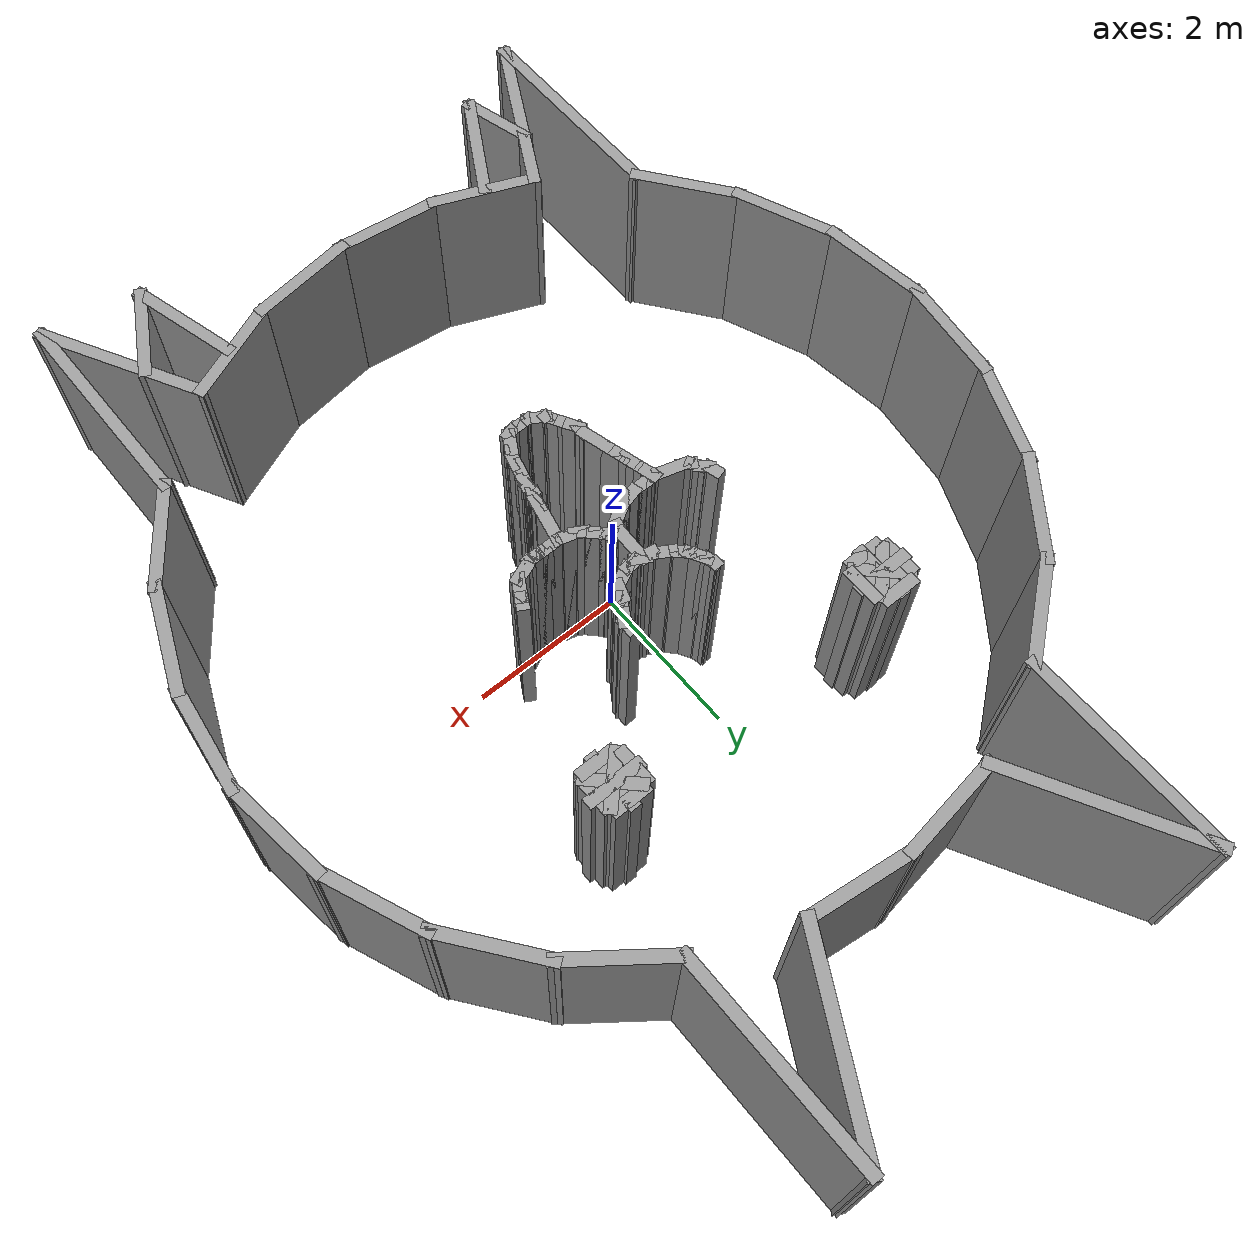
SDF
<?xml version='1.0'?>
<sdf version='1.6'>
  <model name='cat'>
    <pose frame=''>0.253474 0.457983 0 0 -0 0</pose>
    <link name='Wall_107'>
      <collision name='Wall_107_Collision'>
        <geometry>
          <box>
            <size>2.75 0.15 2.5</size>
          </box>
        </geometry>
        <pose frame=''>0 0 1.25 0 -0 0</pose>
      </collision>
      <visual name='Wall_107_Visual'>
        <pose frame=''>0 0 1.25 0 -0 0</pose>
        <geometry>
          <box>
            <size>2.75 0.15 2.5</size>
          </box>
        </geometry>
        <material>
          <script>
            <uri>file://media/materials/scripts/gazebo.material</uri>
            <name>Gazebo/Grey</name>
          </script>
          <ambient>1 1 1 1</ambient>
        </material>
        <meta>
          <layer>0</layer>
        </meta>
      </visual>
      <pose frame=''>3.42947 -5.10717 0 0 -0 -1.5708</pose>
    </link>
    <link name='Wall_108'>
      <collision name='Wall_108_Collision'>
        <geometry>
          <box>
            <size>2.23689 0.15 2.5</size>
          </box>
        </geometry>
        <pose frame=''>0 0 1.25 0 -0 0</pose>
      </collision>
      <visual name='Wall_108_Visual'>
        <pose frame=''>0 0 1.25 0 -0 0</pose>
        <geometry>
          <box>
            <size>2.23689 0.15 2.5</size>
          </box>
        </geometry>
        <material>
          <script>
            <uri>file://media/materials/scripts/gazebo.material</uri>
            <name>Gazebo/Grey</name>
          </script>
          <ambient>1 1 1 1</ambient>
        </material>
        <meta>
          <layer>0</layer>
        </meta>
      </visual>
      <pose frame=''>2.92723 -5.49255 0 0 -0 2.07296</pose>
    </link>
    <link name='Wall_110'>
      <collision name='Wall_110_Collision'>
        <geometry>
          <box>
            <size>2.75 0.15 2.5</size>
          </box>
        </geometry>
        <pose frame=''>0 0 1.25 0 -0 0</pose>
      </collision>
      <visual name='Wall_110_Visual'>
        <pose frame=''>0 0 1.25 0 -0 0</pose>
        <geometry>
          <box>
            <size>2.75 0.15 2.5</size>
          </box>
        </geometry>
        <material>
          <script>
            <uri>file://media/materials/scripts/gazebo.material</uri>
            <name>Gazebo/Grey</name>
          </script>
          <ambient>1 1 1 1</ambient>
        </material>
        <meta>
          <layer>0</layer>
        </meta>
      </visual>
      <pose frame=''>-3.42947 -5.12272 0 0 -0 -1.5708</pose>
    </link>
    <link name='Wall_111'>
      <collision name='Wall_111_Collision'>
        <geometry>
          <box>
            <size>2.25053 0.15 2.5</size>
          </box>
        </geometry>
        <pose frame=''>0 0 1.25 0 -0 0</pose>
      </collision>
      <visual name='Wall_111_Visual'>
        <pose frame=''>0 0 1.25 0 -0 0</pose>
        <geometry>
          <box>
            <size>2.25053 0.15 2.5</size>
          </box>
        </geometry>
        <material>
          <script>
            <uri>file://media/materials/scripts/gazebo.material</uri>
            <name>Gazebo/Grey</name>
          </script>
          <ambient>1 1 1 1</ambient>
        </material>
        <meta>
          <layer>0</layer>
        </meta>
      </visual>
      <pose frame=''>-2.92723 -5.50032 0 0 -0 1.07219</pose>
    </link>
    <link name='Wall_113'>
      <collision name='Wall_113_Collision'>
        <geometry>
          <box>
            <size>1 0.15 2.5</size>
          </box>
        </geometry>
        <pose frame=''>0 0 1.25 0 -0 0</pose>
      </collision>
      <visual name='Wall_113_Visual'>
        <pose frame=''>0 0 1.25 0 -0 0</pose>
        <geometry>
          <box>
            <size>1 0.15 2.5</size>
          </box>
        </geometry>
        <material>
          <script>
            <uri>file://media/materials/scripts/gazebo.material</uri>
            <name>Gazebo/Grey</name>
          </script>
          <ambient>1 1 1 1</ambient>
        </material>
        <meta>
          <layer>0</layer>
        </meta>
      </visual>
      <pose frame=''>-2.64432 -5.59243 0 0 -0 -1.309</pose>
    </link>
    <link name='Wall_114'>
      <collision name='Wall_114_Collision'>
        <geometry>
          <box>
            <size>1.5 0.15 2.5</size>
          </box>
        </geometry>
        <pose frame=''>0 0 1.25 0 -0 0</pose>
      </collision>
      <visual name='Wall_114_Visual'>
        <pose frame=''>0 0 1.25 0 -0 0</pose>
        <geometry>
          <box>
            <size>1.5 0.15 2.5</size>
          </box>
        </geometry>
        <material>
          <script>
            <uri>file://media/materials/scripts/gazebo.material</uri>
            <name>Gazebo/Grey</name>
          </script>
          <ambient>1 1 1 1</ambient>
        </material>
        <meta>
          <layer>0</layer>
        </meta>
      </visual>
      <pose frame=''>-2.19682 -5.41839 0 0 -0 1.0472</pose>
    </link>
    <link name='Wall_118'>
      <collision name='Wall_118_Collision'>
        <geometry>
          <box>
            <size>1.25 0.15 2.5</size>
          </box>
        </geometry>
        <pose frame=''>0 0 1.25 0 -0 0</pose>
      </collision>
      <visual name='Wall_118_Visual'>
        <pose frame=''>0 0 1.25 0 -0 0</pose>
        <geometry>
          <box>
            <size>1.25 0.15 2.5</size>
          </box>
        </geometry>
        <material>
          <script>
            <uri>file://media/materials/scripts/gazebo.material</uri>
            <name>Gazebo/Grey</name>
          </script>
          <ambient>1 1 1 1</ambient>
        </material>
        <meta>
          <layer>0</layer>
        </meta>
      </visual>
      <pose frame=''>2.50531 -5.68932 0 0 -0 -2.0944</pose>
    </link>
    <link name='Wall_119'>
      <collision name='Wall_119_Collision'>
        <geometry>
          <box>
            <size>1.5 0.15 2.5</size>
          </box>
        </geometry>
        <pose frame=''>0 0 1.25 0 -0 0</pose>
      </collision>
      <visual name='Wall_119_Visual'>
        <pose frame=''>0 0 1.25 0 -0 0</pose>
        <geometry>
          <box>
            <size>1.5 0.15 2.5</size>
          </box>
        </geometry>
        <material>
          <script>
            <uri>file://media/materials/scripts/gazebo.material</uri>
            <name>Gazebo/Grey</name>
          </script>
          <ambient>1 1 1 1</ambient>
        </material>
        <meta>
          <layer>0</layer>
        </meta>
      </visual>
      <pose frame=''>2.05561 -5.51364 0 0 -0 1.8326</pose>
    </link>
    <link name='Wall_127'>
      <collision name='Wall_127_Collision'>
        <geometry>
          <box>
            <size>2.75 0.15 2.5</size>
          </box>
        </geometry>
        <pose frame=''>0 0 1.25 0 -0 0</pose>
      </collision>
      <visual name='Wall_127_Visual'>
        <pose frame=''>0 0 1.25 0 -0 0</pose>
        <geometry>
          <box>
            <size>2.75 0.15 2.5</size>
          </box>
        </geometry>
        <material>
          <script>
            <uri>file://media/materials/scripts/gazebo.material</uri>
            <name>Gazebo/Grey</name>
          </script>
          <ambient>1 1 1 1</ambient>
        </material>
        <meta>
          <layer>0</layer>
        </meta>
      </visual>
      <pose frame=''>-2.425 5.12252 0 0 -0 1.5708</pose>
    </link>
    <link name='Wall_128'>
      <collision name='Wall_128_Collision'>
        <geometry>
          <box>
            <size>2.56734 0.15 2.5</size>
          </box>
        </geometry>
        <pose frame=''>0 0 1.25 0 -0 0</pose>
      </collision>
      <visual name='Wall_128_Visual'>
        <pose frame=''>0 0 1.25 0 -0 0</pose>
        <geometry>
          <box>
            <size>2.56734 0.15 2.5</size>
          </box>
        </geometry>
        <material>
          <script>
            <uri>file://media/materials/scripts/gazebo.material</uri>
            <name>Gazebo/Grey</name>
          </script>
          <ambient>1 1 1 1</ambient>
        </material>
        <meta>
          <layer>0</layer>
        </meta>
      </visual>
      <pose frame=''>-1.84014 5.36478 0 0 -0 -1.0657</pose>
    </link>
    <link name='Wall_130'>
      <collision name='Wall_130_Collision'>
        <geometry>
          <box>
            <size>2.75 0.15 2.5</size>
          </box>
        </geometry>
        <pose frame=''>0 0 1.25 0 -0 0</pose>
      </collision>
      <visual name='Wall_130_Visual'>
        <pose frame=''>0 0 1.25 0 -0 0</pose>
        <geometry>
          <box>
            <size>2.75 0.15 2.5</size>
          </box>
        </geometry>
        <material>
          <script>
            <uri>file://media/materials/scripts/gazebo.material</uri>
            <name>Gazebo/Grey</name>
          </script>
          <ambient>1 1 1 1</ambient>
        </material>
        <meta>
          <layer>0</layer>
        </meta>
      </visual>
      <pose frame=''>2.425 5.12252 0 0 -0 1.5708</pose>
    </link>
    <link name='Wall_131'>
      <collision name='Wall_131_Collision'>
        <geometry>
          <box>
            <size>2.56734 0.15 2.5</size>
          </box>
        </geometry>
        <pose frame=''>0 0 1.25 0 -0 0</pose>
      </collision>
      <visual name='Wall_131_Visual'>
        <pose frame=''>0 0 1.25 0 -0 0</pose>
        <geometry>
          <box>
            <size>2.56734 0.15 2.5</size>
          </box>
        </geometry>
        <material>
          <script>
            <uri>file://media/materials/scripts/gazebo.material</uri>
            <name>Gazebo/Grey</name>
          </script>
          <ambient>1 1 1 1</ambient>
        </material>
        <meta>
          <layer>0</layer>
        </meta>
      </visual>
      <pose frame=''>1.84014 5.36478 0 0 -0 -2.07589</pose>
    </link>
    <link name='Wall_139'>
      <collision name='Wall_139_Collision'>
        <geometry>
          <box>
            <size>0.75 0.15 2.5</size>
          </box>
        </geometry>
        <pose frame=''>0 0 1.25 0 -0 0</pose>
      </collision>
      <visual name='Wall_139_Visual'>
        <pose frame=''>0 0 1.25 0 -0 0</pose>
        <geometry>
          <box>
            <size>0.75 0.15 2.5</size>
          </box>
        </geometry>
        <material>
          <script>
            <uri>file://media/materials/scripts/gazebo.material</uri>
            <name>Gazebo/Grey</name>
          </script>
          <ambient>1 1 1 1</ambient>
        </material>
        <meta>
          <layer>0</layer>
        </meta>
      </visual>
      <pose frame=''>-1.94097 2.03692 0 0 -0 0</pose>
    </link>
    <link name='Wall_141'>
      <collision name='Wall_141_Collision'>
        <geometry>
          <box>
            <size>0.75 0.15 2.5</size>
          </box>
        </geometry>
        <pose frame=''>0 0 1.25 0 -0 0</pose>
      </collision>
      <visual name='Wall_141_Visual'>
        <pose frame=''>0 0 1.25 0 -0 0</pose>
        <geometry>
          <box>
            <size>0.75 0.15 2.5</size>
          </box>
        </geometry>
        <material>
          <script>
            <uri>file://media/materials/scripts/gazebo.material</uri>
            <name>Gazebo/Grey</name>
          </script>
          <ambient>1 1 1 1</ambient>
        </material>
        <meta>
          <layer>0</layer>
        </meta>
      </visual>
      <pose frame=''>1.82063 2.03692 0 0 -0 0</pose>
    </link>
    <link name='Wall_143'>
      <collision name='Wall_143_Collision'>
        <geometry>
          <box>
            <size>0.75 0.15 2.5</size>
          </box>
        </geometry>
        <pose frame=''>0 0 1.25 0 -0 0</pose>
      </collision>
      <visual name='Wall_143_Visual'>
        <pose frame=''>0 0 1.25 0 -0 0</pose>
        <geometry>
          <box>
            <size>0.75 0.15 2.5</size>
          </box>
        </geometry>
        <material>
          <script>
            <uri>file://media/materials/scripts/gazebo.material</uri>
            <name>Gazebo/Grey</name>
          </script>
          <ambient>1 1 1 1</ambient>
        </material>
        <meta>
          <layer>0</layer>
        </meta>
      </visual>
      <pose frame=''>-1.93337 2.02695 0 0 -0 -1.5708</pose>
    </link>
    <link name='Wall_145'>
      <collision name='Wall_145_Collision'>
        <geometry>
          <box>
            <size>0.75 0.15 2.5</size>
          </box>
        </geometry>
        <pose frame=''>0 0 1.25 0 -0 0</pose>
      </collision>
      <visual name='Wall_145_Visual'>
        <pose frame=''>0 0 1.25 0 -0 0</pose>
        <geometry>
          <box>
            <size>0.75 0.15 2.5</size>
          </box>
        </geometry>
        <material>
          <script>
            <uri>file://media/materials/scripts/gazebo.material</uri>
            <name>Gazebo/Grey</name>
          </script>
          <ambient>1 1 1 1</ambient>
        </material>
        <meta>
          <layer>0</layer>
        </meta>
      </visual>
      <pose frame=''>1.82824 2.01174 0 0 -0 1.5708</pose>
    </link>
    <link name='Wall_147'>
      <collision name='Wall_147_Collision'>
        <geometry>
          <box>
            <size>0.75 0.15 2.5</size>
          </box>
        </geometry>
        <pose frame=''>0 0 1.25 0 -0 0</pose>
      </collision>
      <visual name='Wall_147_Visual'>
        <pose frame=''>0 0 1.25 0 -0 0</pose>
        <geometry>
          <box>
            <size>0.75 0.15 2.5</size>
          </box>
        </geometry>
        <material>
          <script>
            <uri>file://media/materials/scripts/gazebo.material</uri>
            <name>Gazebo/Grey</name>
          </script>
          <ambient>1 1 1 1</ambient>
        </material>
        <meta>
          <layer>0</layer>
        </meta>
      </visual>
      <pose frame=''>-1.94095 2.02934 0 0 -0 0.785398</pose>
    </link>
    <link name='Wall_149'>
      <collision name='Wall_149_Collision'>
        <geometry>
          <box>
            <size>0.75 0.15 2.5</size>
          </box>
        </geometry>
        <pose frame=''>0 0 1.25 0 -0 0</pose>
      </collision>
      <visual name='Wall_149_Visual'>
        <pose frame=''>0 0 1.25 0 -0 0</pose>
        <geometry>
          <box>
            <size>0.75 0.15 2.5</size>
          </box>
        </geometry>
        <material>
          <script>
            <uri>file://media/materials/scripts/gazebo.material</uri>
            <name>Gazebo/Grey</name>
          </script>
          <ambient>1 1 1 1</ambient>
        </material>
        <meta>
          <layer>0</layer>
        </meta>
      </visual>
      <pose frame=''>-1.94095 2.02693 0 0 -0 -0.785398</pose>
    </link>
    <link name='Wall_151'>
      <collision name='Wall_151_Collision'>
        <geometry>
          <box>
            <size>0.75 0.15 2.5</size>
          </box>
        </geometry>
        <pose frame=''>0 0 1.25 0 -0 0</pose>
      </collision>
      <visual name='Wall_151_Visual'>
        <pose frame=''>0 0 1.25 0 -0 0</pose>
        <geometry>
          <box>
            <size>0.75 0.15 2.5</size>
          </box>
        </geometry>
        <material>
          <script>
            <uri>file://media/materials/scripts/gazebo.material</uri>
            <name>Gazebo/Grey</name>
          </script>
          <ambient>1 1 1 1</ambient>
        </material>
        <meta>
          <layer>0</layer>
        </meta>
      </visual>
      <pose frame=''>1.81186 2.00297 0 0 -0 0.785398</pose>
    </link>
    <link name='Wall_153'>
      <collision name='Wall_153_Collision'>
        <geometry>
          <box>
            <size>0.75 0.15 2.5</size>
          </box>
        </geometry>
        <pose frame=''>0 0 1.25 0 -0 0</pose>
      </collision>
      <visual name='Wall_153_Visual'>
        <pose frame=''>0 0 1.25 0 -0 0</pose>
        <geometry>
          <box>
            <size>0.75 0.15 2.5</size>
          </box>
        </geometry>
        <material>
          <script>
            <uri>file://media/materials/scripts/gazebo.material</uri>
            <name>Gazebo/Grey</name>
          </script>
          <ambient>1 1 1 1</ambient>
        </material>
        <meta>
          <layer>0</layer>
        </meta>
      </visual>
      <pose frame=''>1.82944 2.01814 0 0 -0 -0.785398</pose>
    </link>
    <link name='Wall_155'>
      <collision name='Wall_155_Collision'>
        <geometry>
          <box>
            <size>0.5 0.15 2.5</size>
          </box>
        </geometry>
        <pose frame=''>0 0 1.25 0 -0 0</pose>
      </collision>
      <visual name='Wall_155_Visual'>
        <pose frame=''>0 0 1.25 0 -0 0</pose>
        <geometry>
          <box>
            <size>0.5 0.15 2.5</size>
          </box>
        </geometry>
        <material>
          <script>
            <uri>file://media/materials/scripts/gazebo.material</uri>
            <name>Gazebo/Grey</name>
          </script>
          <ambient>1 1 1 1</ambient>
        </material>
        <meta>
          <layer>0</layer>
        </meta>
      </visual>
      <pose frame=''>-1.92535 2.30938 0 0 -0 0</pose>
    </link>
    <link name='Wall_157'>
      <collision name='Wall_157_Collision'>
        <geometry>
          <box>
            <size>0.5 0.15 2.5</size>
          </box>
        </geometry>
        <pose frame=''>0 0 1.25 0 -0 0</pose>
      </collision>
      <visual name='Wall_157_Visual'>
        <pose frame=''>0 0 1.25 0 -0 0</pose>
        <geometry>
          <box>
            <size>0.5 0.15 2.5</size>
          </box>
        </geometry>
        <material>
          <script>
            <uri>file://media/materials/scripts/gazebo.material</uri>
            <name>Gazebo/Grey</name>
          </script>
          <ambient>1 1 1 1</ambient>
        </material>
        <meta>
          <layer>0</layer>
        </meta>
      </visual>
      <pose frame=''>-1.94293 1.75568 0 0 -0 0</pose>
    </link>
    <link name='Wall_159'>
      <collision name='Wall_159_Collision'>
        <geometry>
          <box>
            <size>0.5 0.15 2.5</size>
          </box>
        </geometry>
        <pose frame=''>0 0 1.25 0 -0 0</pose>
      </collision>
      <visual name='Wall_159_Visual'>
        <pose frame=''>0 0 1.25 0 -0 0</pose>
        <geometry>
          <box>
            <size>0.5 0.15 2.5</size>
          </box>
        </geometry>
        <material>
          <script>
            <uri>file://media/materials/scripts/gazebo.material</uri>
            <name>Gazebo/Grey</name>
          </script>
          <ambient>1 1 1 1</ambient>
        </material>
        <meta>
          <layer>0</layer>
        </meta>
      </visual>
      <pose frame=''>-2.20582 2.01857 0 0 -0 1.5708</pose>
    </link>
    <link name='Wall_163'>
      <collision name='Wall_163_Collision'>
        <geometry>
          <box>
            <size>0.5 0.15 2.5</size>
          </box>
        </geometry>
        <pose frame=''>0 0 1.25 0 -0 0</pose>
      </collision>
      <visual name='Wall_163_Visual'>
        <pose frame=''>0 0 1.25 0 -0 0</pose>
        <geometry>
          <box>
            <size>0.5 0.15 2.5</size>
          </box>
        </geometry>
        <material>
          <script>
            <uri>file://media/materials/scripts/gazebo.material</uri>
            <name>Gazebo/Grey</name>
          </script>
          <ambient>1 1 1 1</ambient>
        </material>
        <meta>
          <layer>0</layer>
        </meta>
      </visual>
      <pose frame=''>-1.6697 2.02012 0 0 -0 -1.5708</pose>
    </link>
    <link name='Wall_165'>
      <collision name='Wall_165_Collision'>
        <geometry>
          <box>
            <size>0.5 0.15 2.5</size>
          </box>
        </geometry>
        <pose frame=''>0 0 1.25 0 -0 0</pose>
      </collision>
      <visual name='Wall_165_Visual'>
        <pose frame=''>0 0 1.25 0 -0 0</pose>
        <geometry>
          <box>
            <size>0.5 0.15 2.5</size>
          </box>
        </geometry>
        <material>
          <script>
            <uri>file://media/materials/scripts/gazebo.material</uri>
            <name>Gazebo/Grey</name>
          </script>
          <ambient>1 1 1 1</ambient>
        </material>
        <meta>
          <layer>0</layer>
        </meta>
      </visual>
      <pose frame=''>1.55578 2.02891 0 0 -0 -1.5708</pose>
    </link>
    <link name='Wall_169'>
      <collision name='Wall_169_Collision'>
        <geometry>
          <box>
            <size>0.5 0.15 2.5</size>
          </box>
        </geometry>
        <pose frame=''>0 0 1.25 0 -0 0</pose>
      </collision>
      <visual name='Wall_169_Visual'>
        <pose frame=''>0 0 1.25 0 -0 0</pose>
        <geometry>
          <box>
            <size>0.5 0.15 2.5</size>
          </box>
        </geometry>
        <material>
          <script>
            <uri>file://media/materials/scripts/gazebo.material</uri>
            <name>Gazebo/Grey</name>
          </script>
          <ambient>1 1 1 1</ambient>
        </material>
        <meta>
          <layer>0</layer>
        </meta>
      </visual>
      <pose frame=''>2.05674 2.00254 0 0 -0 -1.5708</pose>
    </link>
    <link name='Wall_173'>
      <collision name='Wall_173_Collision'>
        <geometry>
          <box>
            <size>0.5 0.15 2.5</size>
          </box>
        </geometry>
        <pose frame=''>0 0 1.25 0 -0 0</pose>
      </collision>
      <visual name='Wall_173_Visual'>
        <pose frame=''>0 0 1.25 0 -0 0</pose>
        <geometry>
          <box>
            <size>0.5 0.15 2.5</size>
          </box>
        </geometry>
        <material>
          <script>
            <uri>file://media/materials/scripts/gazebo.material</uri>
            <name>Gazebo/Grey</name>
          </script>
          <ambient>1 1 1 1</ambient>
        </material>
        <meta>
          <layer>0</layer>
        </meta>
      </visual>
      <pose frame=''>1.81867 2.27422 0 0 -0 0</pose>
    </link>
    <link name='Wall_175'>
      <collision name='Wall_175_Collision'>
        <geometry>
          <box>
            <size>0.5 0.15 2.5</size>
          </box>
        </geometry>
        <pose frame=''>0 0 1.25 0 -0 0</pose>
      </collision>
      <visual name='Wall_175_Visual'>
        <pose frame=''>0 0 1.25 0 -0 0</pose>
        <geometry>
          <box>
            <size>0.5 0.15 2.5</size>
          </box>
        </geometry>
        <material>
          <script>
            <uri>file://media/materials/scripts/gazebo.material</uri>
            <name>Gazebo/Grey</name>
          </script>
          <ambient>1 1 1 1</ambient>
        </material>
        <meta>
          <layer>0</layer>
        </meta>
      </visual>
      <pose frame=''>1.82746 1.75568 0 0 -0 0</pose>
    </link>
    <link name='Wall_180'>
      <collision name='Wall_180_Collision'>
        <geometry>
          <box>
            <size>0.15 0.15 2.5</size>
          </box>
        </geometry>
        <pose frame=''>0 0 1.25 0 -0 0</pose>
      </collision>
      <visual name='Wall_180_Visual'>
        <pose frame=''>0 0 1.25 0 -0 0</pose>
        <geometry>
          <box>
            <size>0.15 0.15 2.5</size>
          </box>
        </geometry>
        <material>
          <script>
            <uri>file://media/materials/scripts/gazebo.material</uri>
            <name>Gazebo/Grey</name>
          </script>
          <ambient>1 1 1 1</ambient>
        </material>
        <meta>
          <layer>0</layer>
        </meta>
      </visual>
      <pose frame=''>-0.621599 0.80645 0 0 -0 0</pose>
    </link>
    <link name='Wall_189'>
      <collision name='Wall_189_Collision'>
        <geometry>
          <box>
            <size>0.25 0.15 2.5</size>
          </box>
        </geometry>
        <pose frame=''>0 0 1.25 0 -0 0</pose>
      </collision>
      <visual name='Wall_189_Visual'>
        <pose frame=''>0 0 1.25 0 -0 0</pose>
        <geometry>
          <box>
            <size>0.25 0.15 2.5</size>
          </box>
        </geometry>
        <material>
          <script>
            <uri>file://media/materials/scripts/gazebo.material</uri>
            <name>Gazebo/Grey</name>
          </script>
          <ambient>1 1 1 1</ambient>
        </material>
        <meta>
          <layer>0</layer>
        </meta>
      </visual>
      <pose frame=''>-0.608658 0.758154 0 0 -0 -1.309</pose>
    </link>
    <link name='Wall_190'>
      <collision name='Wall_190_Collision'>
        <geometry>
          <box>
            <size>0.25 0.15 2.5</size>
          </box>
        </geometry>
        <pose frame=''>0 0 1.25 0 -0 0</pose>
      </collision>
      <visual name='Wall_190_Visual'>
        <pose frame=''>0 0 1.25 0 -0 0</pose>
        <geometry>
          <box>
            <size>0.25 0.15 2.5</size>
          </box>
        </geometry>
        <material>
          <script>
            <uri>file://media/materials/scripts/gazebo.material</uri>
            <name>Gazebo/Grey</name>
          </script>
          <ambient>1 1 1 1</ambient>
        </material>
        <meta>
          <layer>0</layer>
        </meta>
      </visual>
      <pose frame=''>-0.570717 0.666556 0 0 -0 -1.0472</pose>
    </link>
    <link name='Wall_191'>
      <collision name='Wall_191_Collision'>
        <geometry>
          <box>
            <size>0.25 0.15 2.5</size>
          </box>
        </geometry>
        <pose frame=''>0 0 1.25 0 -0 0</pose>
      </collision>
      <visual name='Wall_191_Visual'>
        <pose frame=''>0 0 1.25 0 -0 0</pose>
        <geometry>
          <box>
            <size>0.25 0.15 2.5</size>
          </box>
        </geometry>
        <material>
          <script>
            <uri>file://media/materials/scripts/gazebo.material</uri>
            <name>Gazebo/Grey</name>
          </script>
          <ambient>1 1 1 1</ambient>
        </material>
        <meta>
          <layer>0</layer>
        </meta>
      </visual>
      <pose frame=''>-0.520717 0.579954 0 0 -0 -1.0472</pose>
    </link>
    <link name='Wall_192'>
      <collision name='Wall_192_Collision'>
        <geometry>
          <box>
            <size>0.25 0.15 2.5</size>
          </box>
        </geometry>
        <pose frame=''>0 0 1.25 0 -0 0</pose>
      </collision>
      <visual name='Wall_192_Visual'>
        <pose frame=''>0 0 1.25 0 -0 0</pose>
        <geometry>
          <box>
            <size>0.25 0.15 2.5</size>
          </box>
        </geometry>
        <material>
          <script>
            <uri>file://media/materials/scripts/gazebo.material</uri>
            <name>Gazebo/Grey</name>
          </script>
          <ambient>1 1 1 1</ambient>
        </material>
        <meta>
          <layer>0</layer>
        </meta>
      </visual>
      <pose frame=''>-0.460362 0.501297 0 0 -0 -0.785398</pose>
    </link>
    <link name='Wall_193'>
      <collision name='Wall_193_Collision'>
        <geometry>
          <box>
            <size>0.25 0.15 2.5</size>
          </box>
        </geometry>
        <pose frame=''>0 0 1.25 0 -0 0</pose>
      </collision>
      <visual name='Wall_193_Visual'>
        <pose frame=''>0 0 1.25 0 -0 0</pose>
        <geometry>
          <box>
            <size>0.25 0.15 2.5</size>
          </box>
        </geometry>
        <material>
          <script>
            <uri>file://media/materials/scripts/gazebo.material</uri>
            <name>Gazebo/Grey</name>
          </script>
          <ambient>1 1 1 1</ambient>
        </material>
        <meta>
          <layer>0</layer>
        </meta>
      </visual>
      <pose frame=''>-0.389651 0.430586 0 0 -0 -0.785398</pose>
    </link>
    <link name='Wall_194'>
      <collision name='Wall_194_Collision'>
        <geometry>
          <box>
            <size>0.25 0.15 2.5</size>
          </box>
        </geometry>
        <pose frame=''>0 0 1.25 0 -0 0</pose>
      </collision>
      <visual name='Wall_194_Visual'>
        <pose frame=''>0 0 1.25 0 -0 0</pose>
        <geometry>
          <box>
            <size>0.25 0.15 2.5</size>
          </box>
        </geometry>
        <material>
          <script>
            <uri>file://media/materials/scripts/gazebo.material</uri>
            <name>Gazebo/Grey</name>
          </script>
          <ambient>1 1 1 1</ambient>
        </material>
        <meta>
          <layer>0</layer>
        </meta>
      </visual>
      <pose frame=''>-0.310995 0.370231 0 0 -0 -0.523599</pose>
    </link>
    <link name='Wall_195'>
      <collision name='Wall_195_Collision'>
        <geometry>
          <box>
            <size>0.25 0.15 2.5</size>
          </box>
        </geometry>
        <pose frame=''>0 0 1.25 0 -0 0</pose>
      </collision>
      <visual name='Wall_195_Visual'>
        <pose frame=''>0 0 1.25 0 -0 0</pose>
        <geometry>
          <box>
            <size>0.25 0.15 2.5</size>
          </box>
        </geometry>
        <material>
          <script>
            <uri>file://media/materials/scripts/gazebo.material</uri>
            <name>Gazebo/Grey</name>
          </script>
          <ambient>1 1 1 1</ambient>
        </material>
        <meta>
          <layer>0</layer>
        </meta>
      </visual>
      <pose frame=''>-0.224392 0.320231 0 0 -0 -0.523599</pose>
    </link>
    <link name='Wall_196'>
      <collision name='Wall_196_Collision'>
        <geometry>
          <box>
            <size>0.1705 0.15 2.5</size>
          </box>
        </geometry>
        <pose frame=''>0 0 1.25 0 -0 0</pose>
      </collision>
      <visual name='Wall_196_Visual'>
        <pose frame=''>0 0 1.25 0 -0 0</pose>
        <geometry>
          <box>
            <size>0.1705 0.15 2.5</size>
          </box>
        </geometry>
        <material>
          <script>
            <uri>file://media/materials/scripts/gazebo.material</uri>
            <name>Gazebo/Grey</name>
          </script>
          <ambient>1 1 1 1</ambient>
        </material>
        <meta>
          <layer>0</layer>
        </meta>
      </visual>
      <pose frame=''>-0.183272 0.285392 0 0 -0 -1.7889</pose>
    </link>
    <link name='Wall_197'>
      <collision name='Wall_197_Collision'>
        <geometry>
          <box>
            <size>0.25 0.15 2.5</size>
          </box>
        </geometry>
        <pose frame=''>0 0 1.25 0 -0 0</pose>
      </collision>
      <visual name='Wall_197_Visual'>
        <pose frame=''>0 0 1.25 0 -0 0</pose>
        <geometry>
          <box>
            <size>0.25 0.15 2.5</size>
          </box>
        </geometry>
        <material>
          <script>
            <uri>file://media/materials/scripts/gazebo.material</uri>
            <name>Gazebo/Grey</name>
          </script>
          <ambient>1 1 1 1</ambient>
        </material>
        <meta>
          <layer>0</layer>
        </meta>
      </visual>
      <pose frame=''>-0.125345 0.275552 0 0 -0 0</pose>
    </link>
    <link name='Wall_198'>
      <collision name='Wall_198_Collision'>
        <geometry>
          <box>
            <size>0.253124 0.15 2.5</size>
          </box>
        </geometry>
        <pose frame=''>0 0 1.25 0 -0 0</pose>
      </collision>
      <visual name='Wall_198_Visual'>
        <pose frame=''>0 0 1.25 0 -0 0</pose>
        <geometry>
          <box>
            <size>0.253124 0.15 2.5</size>
          </box>
        </geometry>
        <material>
          <script>
            <uri>file://media/materials/scripts/gazebo.material</uri>
            <name>Gazebo/Grey</name>
          </script>
          <ambient>1 1 1 1</ambient>
        </material>
        <meta>
          <layer>0</layer>
        </meta>
      </visual>
      <pose frame=''>-0.040506 0.250285 0 0 -0 -0.512143</pose>
    </link>
    <link name='Wall_199'>
      <collision name='Wall_199_Collision'>
        <geometry>
          <box>
            <size>0.216726 0.15 2.5</size>
          </box>
        </geometry>
        <pose frame=''>0 0 1.25 0 -0 0</pose>
      </collision>
      <visual name='Wall_199_Visual'>
        <pose frame=''>0 0 1.25 0 -0 0</pose>
        <geometry>
          <box>
            <size>0.216726 0.15 2.5</size>
          </box>
        </geometry>
        <material>
          <script>
            <uri>file://media/materials/scripts/gazebo.material</uri>
            <name>Gazebo/Grey</name>
          </script>
          <ambient>1 1 1 1</ambient>
        </material>
        <meta>
          <layer>0</layer>
        </meta>
      </visual>
      <pose frame=''>-0.02812 0.227851 0 0 -0 -2.92182</pose>
    </link>
    <link name='Wall_200'>
      <collision name='Wall_200_Collision'>
        <geometry>
          <box>
            <size>0.353108 0.15 2.5</size>
          </box>
        </geometry>
        <pose frame=''>0 0 1.25 0 -0 0</pose>
      </collision>
      <visual name='Wall_200_Visual'>
        <pose frame=''>0 0 1.25 0 -0 0</pose>
        <geometry>
          <box>
            <size>0.353108 0.15 2.5</size>
          </box>
        </geometry>
        <material>
          <script>
            <uri>file://media/materials/scripts/gazebo.material</uri>
            <name>Gazebo/Grey</name>
          </script>
          <ambient>1 1 1 1</ambient>
        </material>
        <meta>
          <layer>0</layer>
        </meta>
      </visual>
      <pose frame=''>0.040371 0.240772 0 0 -0 0.099496</pose>
    </link>
    <link name='Wall_201'>
      <collision name='Wall_201_Collision'>
        <geometry>
          <box>
            <size>0.39855 0.15 2.5</size>
          </box>
        </geometry>
        <pose frame=''>0 0 1.25 0 -0 0</pose>
      </collision>
      <visual name='Wall_201_Visual'>
        <pose frame=''>0 0 1.25 0 -0 0</pose>
        <geometry>
          <box>
            <size>0.39855 0.15 2.5</size>
          </box>
        </geometry>
        <material>
          <script>
            <uri>file://media/materials/scripts/gazebo.material</uri>
            <name>Gazebo/Grey</name>
          </script>
          <ambient>1 1 1 1</ambient>
        </material>
        <meta>
          <layer>0</layer>
        </meta>
      </visual>
      <pose frame=''>0.252581 0.296322 0 0 -0 0.463577</pose>
    </link>
    <link name='Wall_202'>
      <collision name='Wall_202_Collision'>
        <geometry>
          <box>
            <size>0.300203 0.15 2.5</size>
          </box>
        </geometry>
        <pose frame=''>0 0 1.25 0 -0 0</pose>
      </collision>
      <visual name='Wall_202_Visual'>
        <pose frame=''>0 0 1.25 0 -0 0</pose>
        <geometry>
          <box>
            <size>0.300203 0.15 2.5</size>
          </box>
        </geometry>
        <material>
          <script>
            <uri>file://media/materials/scripts/gazebo.material</uri>
            <name>Gazebo/Grey</name>
          </script>
          <ambient>1 1 1 1</ambient>
        </material>
        <meta>
          <layer>0</layer>
        </meta>
      </visual>
      <pose frame=''>0.388988 0.412515 0 0 -0 1.22793</pose>
    </link>
    <link name='Wall_203'>
      <collision name='Wall_203_Collision'>
        <geometry>
          <box>
            <size>0.25 0.15 2.5</size>
          </box>
        </geometry>
        <pose frame=''>0 0 1.25 0 -0 0</pose>
      </collision>
      <visual name='Wall_203_Visual'>
        <pose frame=''>0 0 1.25 0 -0 0</pose>
        <geometry>
          <box>
            <size>0.25 0.15 2.5</size>
          </box>
        </geometry>
        <material>
          <script>
            <uri>file://media/materials/scripts/gazebo.material</uri>
            <name>Gazebo/Grey</name>
          </script>
          <ambient>1 1 1 1</ambient>
        </material>
        <meta>
          <layer>0</layer>
        </meta>
      </visual>
      <pose frame=''>0.449591 0.5186 0 0 -0 0.785398</pose>
    </link>
    <link name='Wall_204'>
      <collision name='Wall_204_Collision'>
        <geometry>
          <box>
            <size>0.25 0.15 2.5</size>
          </box>
        </geometry>
        <pose frame=''>0 0 1.25 0 -0 0</pose>
      </collision>
      <visual name='Wall_204_Visual'>
        <pose frame=''>0 0 1.25 0 -0 0</pose>
        <geometry>
          <box>
            <size>0.25 0.15 2.5</size>
          </box>
        </geometry>
        <material>
          <script>
            <uri>file://media/materials/scripts/gazebo.material</uri>
            <name>Gazebo/Grey</name>
          </script>
          <ambient>1 1 1 1</ambient>
        </material>
        <meta>
          <layer>0</layer>
        </meta>
      </visual>
      <pose frame=''>0.509947 0.597257 0 0 -0 1.0472</pose>
    </link>
    <link name='Wall_205'>
      <collision name='Wall_205_Collision'>
        <geometry>
          <box>
            <size>0.25 0.15 2.5</size>
          </box>
        </geometry>
        <pose frame=''>0 0 1.25 0 -0 0</pose>
      </collision>
      <visual name='Wall_205_Visual'>
        <pose frame=''>0 0 1.25 0 -0 0</pose>
        <geometry>
          <box>
            <size>0.25 0.15 2.5</size>
          </box>
        </geometry>
        <material>
          <script>
            <uri>file://media/materials/scripts/gazebo.material</uri>
            <name>Gazebo/Grey</name>
          </script>
          <ambient>1 1 1 1</ambient>
        </material>
        <meta>
          <layer>0</layer>
        </meta>
      </visual>
      <pose frame=''>0.559947 0.683859 0 0 -0 1.0472</pose>
    </link>
    <link name='Wall_206'>
      <collision name='Wall_206_Collision'>
        <geometry>
          <box>
            <size>0.25 0.15 2.5</size>
          </box>
        </geometry>
        <pose frame=''>0 0 1.25 0 -0 0</pose>
      </collision>
      <visual name='Wall_206_Visual'>
        <pose frame=''>0 0 1.25 0 -0 0</pose>
        <geometry>
          <box>
            <size>0.25 0.15 2.5</size>
          </box>
        </geometry>
        <material>
          <script>
            <uri>file://media/materials/scripts/gazebo.material</uri>
            <name>Gazebo/Grey</name>
          </script>
          <ambient>1 1 1 1</ambient>
        </material>
        <meta>
          <layer>0</layer>
        </meta>
      </visual>
      <pose frame=''>0.584947 0.777161 0 0 -0 1.5708</pose>
    </link>
    <link name='Wall_216'>
      <collision name='Wall_216_Collision'>
        <geometry>
          <box>
            <size>0.507922 0.15 2.5</size>
          </box>
        </geometry>
        <pose frame=''>0 0 1.25 0 -0 0</pose>
      </collision>
      <visual name='Wall_216_Visual'>
        <pose frame=''>0 0 1.25 0 -0 0</pose>
        <geometry>
          <box>
            <size>0.507922 0.15 2.5</size>
          </box>
        </geometry>
        <material>
          <script>
            <uri>file://media/materials/scripts/gazebo.material</uri>
            <name>Gazebo/Grey</name>
          </script>
          <ambient>1 1 1 1</ambient>
        </material>
        <meta>
          <layer>0</layer>
        </meta>
      </visual>
      <pose frame=''>-0.06828 0.051885 0 0 -0 -1.61327</pose>
    </link>
    <link name='Wall_217'>
      <collision name='Wall_217_Collision'>
        <geometry>
          <box>
            <size>0.25 0.15 2.5</size>
          </box>
        </geometry>
        <pose frame=''>0 0 1.25 0 -0 0</pose>
      </collision>
      <visual name='Wall_217_Visual'>
        <pose frame=''>0 0 1.25 0 -0 0</pose>
        <geometry>
          <box>
            <size>0.25 0.15 2.5</size>
          </box>
        </geometry>
        <material>
          <script>
            <uri>file://media/materials/scripts/gazebo.material</uri>
            <name>Gazebo/Grey</name>
          </script>
          <ambient>1 1 1 1</ambient>
        </material>
        <meta>
          <layer>0</layer>
        </meta>
      </visual>
      <pose frame=''>-0.085021 -0.175211 0 0 -0 -1.8326</pose>
    </link>
    <link name='Wall_218'>
      <collision name='Wall_218_Collision'>
        <geometry>
          <box>
            <size>0.234051 0.15 2.5</size>
          </box>
        </geometry>
        <pose frame=''>0 0 1.25 0 -0 0</pose>
      </collision>
      <visual name='Wall_218_Visual'>
        <pose frame=''>0 0 1.25 0 -0 0</pose>
        <geometry>
          <box>
            <size>0.234051 0.15 2.5</size>
          </box>
        </geometry>
        <material>
          <script>
            <uri>file://media/materials/scripts/gazebo.material</uri>
            <name>Gazebo/Grey</name>
          </script>
          <ambient>1 1 1 1</ambient>
        </material>
        <meta>
          <layer>0</layer>
        </meta>
      </visual>
      <pose frame=''>-0.129517 -0.255063 0 0 -0 -2.29222</pose>
    </link>
    <link name='Wall_219'>
      <collision name='Wall_219_Collision'>
        <geometry>
          <box>
            <size>0.25 0.15 2.5</size>
          </box>
        </geometry>
        <pose frame=''>0 0 1.25 0 -0 0</pose>
      </collision>
      <visual name='Wall_219_Visual'>
        <pose frame=''>0 0 1.25 0 -0 0</pose>
        <geometry>
          <box>
            <size>0.25 0.15 2.5</size>
          </box>
        </geometry>
        <material>
          <script>
            <uri>file://media/materials/scripts/gazebo.material</uri>
            <name>Gazebo/Grey</name>
          </script>
          <ambient>1 1 1 1</ambient>
        </material>
        <meta>
          <layer>0</layer>
        </meta>
      </visual>
      <pose frame=''>-0.200575 -0.311619 0 0 -0 -2.61799</pose>
    </link>
    <link name='Wall_220'>
      <collision name='Wall_220_Collision'>
        <geometry>
          <box>
            <size>0.25 0.15 2.5</size>
          </box>
        </geometry>
        <pose frame=''>0 0 1.25 0 -0 0</pose>
      </collision>
      <visual name='Wall_220_Visual'>
        <pose frame=''>0 0 1.25 0 -0 0</pose>
        <geometry>
          <box>
            <size>0.25 0.15 2.5</size>
          </box>
        </geometry>
        <material>
          <script>
            <uri>file://media/materials/scripts/gazebo.material</uri>
            <name>Gazebo/Grey</name>
          </script>
          <ambient>1 1 1 1</ambient>
        </material>
        <meta>
          <layer>0</layer>
        </meta>
      </visual>
      <pose frame=''>-0.287177 -0.361619 0 0 -0 -2.61799</pose>
    </link>
    <link name='Wall_221'>
      <collision name='Wall_221_Collision'>
        <geometry>
          <box>
            <size>0.25 0.15 2.5</size>
          </box>
        </geometry>
        <pose frame=''>0 0 1.25 0 -0 0</pose>
      </collision>
      <visual name='Wall_221_Visual'>
        <pose frame=''>0 0 1.25 0 -0 0</pose>
        <geometry>
          <box>
            <size>0.25 0.15 2.5</size>
          </box>
        </geometry>
        <material>
          <script>
            <uri>file://media/materials/scripts/gazebo.material</uri>
            <name>Gazebo/Grey</name>
          </script>
          <ambient>1 1 1 1</ambient>
        </material>
        <meta>
          <layer>0</layer>
        </meta>
      </visual>
      <pose frame=''>-0.378775 -0.39956 0 0 -0 -2.87979</pose>
    </link>
    <link name='Wall_222'>
      <collision name='Wall_222_Collision'>
        <geometry>
          <box>
            <size>0.25 0.15 2.5</size>
          </box>
        </geometry>
        <pose frame=''>0 0 1.25 0 -0 0</pose>
      </collision>
      <visual name='Wall_222_Visual'>
        <pose frame=''>0 0 1.25 0 -0 0</pose>
        <geometry>
          <box>
            <size>0.25 0.15 2.5</size>
          </box>
        </geometry>
        <material>
          <script>
            <uri>file://media/materials/scripts/gazebo.material</uri>
            <name>Gazebo/Grey</name>
          </script>
          <ambient>1 1 1 1</ambient>
        </material>
        <meta>
          <layer>0</layer>
        </meta>
      </visual>
      <pose frame=''>-0.475367 -0.425442 0 0 -0 -2.87979</pose>
    </link>
    <link name='Wall_223'>
      <collision name='Wall_223_Collision'>
        <geometry>
          <box>
            <size>0.25 0.15 2.5</size>
          </box>
        </geometry>
        <pose frame=''>0 0 1.25 0 -0 0</pose>
      </collision>
      <visual name='Wall_223_Visual'>
        <pose frame=''>0 0 1.25 0 -0 0</pose>
        <geometry>
          <box>
            <size>0.25 0.15 2.5</size>
          </box>
        </geometry>
        <material>
          <script>
            <uri>file://media/materials/scripts/gazebo.material</uri>
            <name>Gazebo/Grey</name>
          </script>
          <ambient>1 1 1 1</ambient>
        </material>
        <meta>
          <layer>0</layer>
        </meta>
      </visual>
      <pose frame=''>-0.573664 -0.438383 0 0 -0 3.14159</pose>
    </link>
    <link name='Wall_224'>
      <collision name='Wall_224_Collision'>
        <geometry>
          <box>
            <size>0.25 0.15 2.5</size>
          </box>
        </geometry>
        <pose frame=''>0 0 1.25 0 -0 0</pose>
      </collision>
      <visual name='Wall_224_Visual'>
        <pose frame=''>0 0 1.25 0 -0 0</pose>
        <geometry>
          <box>
            <size>0.25 0.15 2.5</size>
          </box>
        </geometry>
        <material>
          <script>
            <uri>file://media/materials/scripts/gazebo.material</uri>
            <name>Gazebo/Grey</name>
          </script>
          <ambient>1 1 1 1</ambient>
        </material>
        <meta>
          <layer>0</layer>
        </meta>
      </visual>
      <pose frame=''>-0.673664 -0.438383 0 0 -0 3.14159</pose>
    </link>
    <link name='Wall_225'>
      <collision name='Wall_225_Collision'>
        <geometry>
          <box>
            <size>0.25 0.15 2.5</size>
          </box>
        </geometry>
        <pose frame=''>0 0 1.25 0 -0 0</pose>
      </collision>
      <visual name='Wall_225_Visual'>
        <pose frame=''>0 0 1.25 0 -0 0</pose>
        <geometry>
          <box>
            <size>0.25 0.15 2.5</size>
          </box>
        </geometry>
        <material>
          <script>
            <uri>file://media/materials/scripts/gazebo.material</uri>
            <name>Gazebo/Grey</name>
          </script>
          <ambient>1 1 1 1</ambient>
        </material>
        <meta>
          <layer>0</layer>
        </meta>
      </visual>
      <pose frame=''>-0.773664 -0.441993 0 0 -0 -3.0695</pose>
    </link>
    <link name='Wall_226'>
      <collision name='Wall_226_Collision'>
        <geometry>
          <box>
            <size>0.501938 0.15 2.5</size>
          </box>
        </geometry>
        <pose frame=''>0 0 1.25 0 -0 0</pose>
      </collision>
      <visual name='Wall_226_Visual'>
        <pose frame=''>0 0 1.25 0 -0 0</pose>
        <geometry>
          <box>
            <size>0.501938 0.15 2.5</size>
          </box>
        </geometry>
        <material>
          <script>
            <uri>file://media/materials/scripts/gazebo.material</uri>
            <name>Gazebo/Grey</name>
          </script>
          <ambient>1 1 1 1</ambient>
        </material>
        <meta>
          <layer>0</layer>
        </meta>
      </visual>
      <pose frame=''>-0.992701 -0.3967 0 0 -0 2.85997</pose>
    </link>
    <link name='Wall_227'>
      <collision name='Wall_227_Collision'>
        <geometry>
          <box>
            <size>0.25 0.15 2.5</size>
          </box>
        </geometry>
        <pose frame=''>0 0 1.25 0 -0 0</pose>
      </collision>
      <visual name='Wall_227_Visual'>
        <pose frame=''>0 0 1.25 0 -0 0</pose>
        <geometry>
          <box>
            <size>0.25 0.15 2.5</size>
          </box>
        </geometry>
        <material>
          <script>
            <uri>file://media/materials/scripts/gazebo.material</uri>
            <name>Gazebo/Grey</name>
          </script>
          <ambient>1 1 1 1</ambient>
        </material>
        <meta>
          <layer>0</layer>
        </meta>
      </visual>
      <pose frame=''>-1.20504 -0.322796 0 0 -0 2.61799</pose>
    </link>
    <link name='Wall_228'>
      <collision name='Wall_228_Collision'>
        <geometry>
          <box>
            <size>0.25 0.15 2.5</size>
          </box>
        </geometry>
        <pose frame=''>0 0 1.25 0 -0 0</pose>
      </collision>
      <visual name='Wall_228_Visual'>
        <pose frame=''>0 0 1.25 0 -0 0</pose>
        <geometry>
          <box>
            <size>0.25 0.15 2.5</size>
          </box>
        </geometry>
        <material>
          <script>
            <uri>file://media/materials/scripts/gazebo.material</uri>
            <name>Gazebo/Grey</name>
          </script>
          <ambient>1 1 1 1</ambient>
        </material>
        <meta>
          <layer>0</layer>
        </meta>
      </visual>
      <pose frame=''>-1.27334 -0.254495 0 0 -0 2.0944</pose>
    </link>
    <link name='Wall_229'>
      <collision name='Wall_229_Collision'>
        <geometry>
          <box>
            <size>0.25 0.15 2.5</size>
          </box>
        </geometry>
        <pose frame=''>0 0 1.25 0 -0 0</pose>
      </collision>
      <visual name='Wall_229_Visual'>
        <pose frame=''>0 0 1.25 0 -0 0</pose>
        <geometry>
          <box>
            <size>0.25 0.15 2.5</size>
          </box>
        </geometry>
        <material>
          <script>
            <uri>file://media/materials/scripts/gazebo.material</uri>
            <name>Gazebo/Grey</name>
          </script>
          <ambient>1 1 1 1</ambient>
        </material>
        <meta>
          <layer>0</layer>
        </meta>
      </visual>
      <pose frame=''>-1.3337 -0.175838 0 0 -0 2.35619</pose>
    </link>
    <link name='Wall_230'>
      <collision name='Wall_230_Collision'>
        <geometry>
          <box>
            <size>0.25 0.15 2.5</size>
          </box>
        </geometry>
        <pose frame=''>0 0 1.25 0 -0 0</pose>
      </collision>
      <visual name='Wall_230_Visual'>
        <pose frame=''>0 0 1.25 0 -0 0</pose>
        <geometry>
          <box>
            <size>0.25 0.15 2.5</size>
          </box>
        </geometry>
        <material>
          <script>
            <uri>file://media/materials/scripts/gazebo.material</uri>
            <name>Gazebo/Grey</name>
          </script>
          <ambient>1 1 1 1</ambient>
        </material>
        <meta>
          <layer>0</layer>
        </meta>
      </visual>
      <pose frame=''>-1.38199 -0.092186 0 0 -0 1.8326</pose>
    </link>
    <link name='Wall_257'>
      <collision name='Wall_257_Collision'>
        <geometry>
          <box>
            <size>0.25 0.15 2.5</size>
          </box>
        </geometry>
        <pose frame=''>0 0 1.25 0 -0 0</pose>
      </collision>
      <visual name='Wall_257_Visual'>
        <pose frame=''>0 0 1.25 0 -0 0</pose>
        <geometry>
          <box>
            <size>0.25 0.15 2.5</size>
          </box>
        </geometry>
        <material>
          <script>
            <uri>file://media/materials/scripts/gazebo.material</uri>
            <name>Gazebo/Grey</name>
          </script>
          <ambient>1 1 1 1</ambient>
        </material>
        <meta>
          <layer>0</layer>
        </meta>
      </visual>
      <pose frame=''>-0.028778 -0.151915 0 0 -0 -0.523599</pose>
    </link>
    <link name='Wall_258'>
      <collision name='Wall_258_Collision'>
        <geometry>
          <box>
            <size>0.25 0.15 2.5</size>
          </box>
        </geometry>
        <pose frame=''>0 0 1.25 0 -0 0</pose>
      </collision>
      <visual name='Wall_258_Visual'>
        <pose frame=''>0 0 1.25 0 -0 0</pose>
        <geometry>
          <box>
            <size>0.25 0.15 2.5</size>
          </box>
        </geometry>
        <material>
          <script>
            <uri>file://media/materials/scripts/gazebo.material</uri>
            <name>Gazebo/Grey</name>
          </script>
          <ambient>1 1 1 1</ambient>
        </material>
        <meta>
          <layer>0</layer>
        </meta>
      </visual>
      <pose frame=''>0.049878 -0.21227 0 0 -0 -0.785398</pose>
    </link>
    <link name='Wall_259'>
      <collision name='Wall_259_Collision'>
        <geometry>
          <box>
            <size>0.25 0.15 2.5</size>
          </box>
        </geometry>
        <pose frame=''>0 0 1.25 0 -0 0</pose>
      </collision>
      <visual name='Wall_259_Visual'>
        <pose frame=''>0 0 1.25 0 -0 0</pose>
        <geometry>
          <box>
            <size>0.25 0.15 2.5</size>
          </box>
        </geometry>
        <material>
          <script>
            <uri>file://media/materials/scripts/gazebo.material</uri>
            <name>Gazebo/Grey</name>
          </script>
          <ambient>1 1 1 1</ambient>
        </material>
        <meta>
          <layer>0</layer>
        </meta>
      </visual>
      <pose frame=''>0.120589 -0.282981 0 0 -0 -0.785398</pose>
    </link>
    <link name='Wall_260'>
      <collision name='Wall_260_Collision'>
        <geometry>
          <box>
            <size>0.25 0.15 2.5</size>
          </box>
        </geometry>
        <pose frame=''>0 0 1.25 0 -0 0</pose>
      </collision>
      <visual name='Wall_260_Visual'>
        <pose frame=''>0 0 1.25 0 -0 0</pose>
        <geometry>
          <box>
            <size>0.25 0.15 2.5</size>
          </box>
        </geometry>
        <material>
          <script>
            <uri>file://media/materials/scripts/gazebo.material</uri>
            <name>Gazebo/Grey</name>
          </script>
          <ambient>1 1 1 1</ambient>
        </material>
        <meta>
          <layer>0</layer>
        </meta>
      </visual>
      <pose frame=''>0.1913 -0.353691 0 0 -0 -0.785398</pose>
    </link>
    <link name='Wall_261'>
      <collision name='Wall_261_Collision'>
        <geometry>
          <box>
            <size>0.25 0.15 2.5</size>
          </box>
        </geometry>
        <pose frame=''>0 0 1.25 0 -0 0</pose>
      </collision>
      <visual name='Wall_261_Visual'>
        <pose frame=''>0 0 1.25 0 -0 0</pose>
        <geometry>
          <box>
            <size>0.25 0.15 2.5</size>
          </box>
        </geometry>
        <material>
          <script>
            <uri>file://media/materials/scripts/gazebo.material</uri>
            <name>Gazebo/Grey</name>
          </script>
          <ambient>1 1 1 1</ambient>
        </material>
        <meta>
          <layer>0</layer>
        </meta>
      </visual>
      <pose frame=''>0.269956 -0.414047 0 0 -0 -0.523599</pose>
    </link>
    <link name='Wall_262'>
      <collision name='Wall_262_Collision'>
        <geometry>
          <box>
            <size>0.25 0.15 2.5</size>
          </box>
        </geometry>
        <pose frame=''>0 0 1.25 0 -0 0</pose>
      </collision>
      <visual name='Wall_262_Visual'>
        <pose frame=''>0 0 1.25 0 -0 0</pose>
        <geometry>
          <box>
            <size>0.25 0.15 2.5</size>
          </box>
        </geometry>
        <material>
          <script>
            <uri>file://media/materials/scripts/gazebo.material</uri>
            <name>Gazebo/Grey</name>
          </script>
          <ambient>1 1 1 1</ambient>
        </material>
        <meta>
          <layer>0</layer>
        </meta>
      </visual>
      <pose frame=''>0.361554 -0.451988 0 0 -0 -0.261799</pose>
    </link>
    <link name='Wall_263'>
      <collision name='Wall_263_Collision'>
        <geometry>
          <box>
            <size>0.25 0.15 2.5</size>
          </box>
        </geometry>
        <pose frame=''>0 0 1.25 0 -0 0</pose>
      </collision>
      <visual name='Wall_263_Visual'>
        <pose frame=''>0 0 1.25 0 -0 0</pose>
        <geometry>
          <box>
            <size>0.25 0.15 2.5</size>
          </box>
        </geometry>
        <material>
          <script>
            <uri>file://media/materials/scripts/gazebo.material</uri>
            <name>Gazebo/Grey</name>
          </script>
          <ambient>1 1 1 1</ambient>
        </material>
        <meta>
          <layer>0</layer>
        </meta>
      </visual>
      <pose frame=''>0.458146 -0.47787 0 0 -0 -0.261799</pose>
    </link>
    <link name='Wall_264'>
      <collision name='Wall_264_Collision'>
        <geometry>
          <box>
            <size>0.25 0.15 2.5</size>
          </box>
        </geometry>
        <pose frame=''>0 0 1.25 0 -0 0</pose>
      </collision>
      <visual name='Wall_264_Visual'>
        <pose frame=''>0 0 1.25 0 -0 0</pose>
        <geometry>
          <box>
            <size>0.25 0.15 2.5</size>
          </box>
        </geometry>
        <material>
          <script>
            <uri>file://media/materials/scripts/gazebo.material</uri>
            <name>Gazebo/Grey</name>
          </script>
          <ambient>1 1 1 1</ambient>
        </material>
        <meta>
          <layer>0</layer>
        </meta>
      </visual>
      <pose frame=''>0.556443 -0.490811 0 0 -0 0</pose>
    </link>
    <link name='Wall_265'>
      <collision name='Wall_265_Collision'>
        <geometry>
          <box>
            <size>0.25 0.15 2.5</size>
          </box>
        </geometry>
        <pose frame=''>0 0 1.25 0 -0 0</pose>
      </collision>
      <visual name='Wall_265_Visual'>
        <pose frame=''>0 0 1.25 0 -0 0</pose>
        <geometry>
          <box>
            <size>0.25 0.15 2.5</size>
          </box>
        </geometry>
        <material>
          <script>
            <uri>file://media/materials/scripts/gazebo.material</uri>
            <name>Gazebo/Grey</name>
          </script>
          <ambient>1 1 1 1</ambient>
        </material>
        <meta>
          <layer>0</layer>
        </meta>
      </visual>
      <pose frame=''>0.656443 -0.490811 0 0 -0 0</pose>
    </link>
    <link name='Wall_266'>
      <collision name='Wall_266_Collision'>
        <geometry>
          <box>
            <size>0.25 0.15 2.5</size>
          </box>
        </geometry>
        <pose frame=''>0 0 1.25 0 -0 0</pose>
      </collision>
      <visual name='Wall_266_Visual'>
        <pose frame=''>0 0 1.25 0 -0 0</pose>
        <geometry>
          <box>
            <size>0.25 0.15 2.5</size>
          </box>
        </geometry>
        <material>
          <script>
            <uri>file://media/materials/scripts/gazebo.material</uri>
            <name>Gazebo/Grey</name>
          </script>
          <ambient>1 1 1 1</ambient>
        </material>
        <meta>
          <layer>0</layer>
        </meta>
      </visual>
      <pose frame=''>0.756443 -0.490811 0 0 -0 0</pose>
    </link>
    <link name='Wall_267'>
      <collision name='Wall_267_Collision'>
        <geometry>
          <box>
            <size>0.15 0.15 2.5</size>
          </box>
        </geometry>
        <pose frame=''>0 0 1.25 0 -0 0</pose>
      </collision>
      <visual name='Wall_267_Visual'>
        <pose frame=''>0 0 1.25 0 -0 0</pose>
        <geometry>
          <box>
            <size>0.15 0.15 2.5</size>
          </box>
        </geometry>
        <material>
          <script>
            <uri>file://media/materials/scripts/gazebo.material</uri>
            <name>Gazebo/Grey</name>
          </script>
          <ambient>1 1 1 1</ambient>
        </material>
        <meta>
          <layer>0</layer>
        </meta>
      </visual>
      <pose frame=''>0.806443 -0.490811 0 0 -0 0</pose>
    </link>
    <link name='Wall_268'>
      <collision name='Wall_268_Collision'>
        <geometry>
          <box>
            <size>0.25 0.15 2.5</size>
          </box>
        </geometry>
        <pose frame=''>0 0 1.25 0 -0 0</pose>
      </collision>
      <visual name='Wall_268_Visual'>
        <pose frame=''>0 0 1.25 0 -0 0</pose>
        <geometry>
          <box>
            <size>0.25 0.15 2.5</size>
          </box>
        </geometry>
        <material>
          <script>
            <uri>file://media/materials/scripts/gazebo.material</uri>
            <name>Gazebo/Grey</name>
          </script>
          <ambient>1 1 1 1</ambient>
        </material>
        <meta>
          <layer>0</layer>
        </meta>
      </visual>
      <pose frame=''>0.856443 -0.490811 0 0 -0 0</pose>
    </link>
    <link name='Wall_269'>
      <collision name='Wall_269_Collision'>
        <geometry>
          <box>
            <size>0.236349 0.15 2.5</size>
          </box>
        </geometry>
        <pose frame=''>0 0 1.25 0 -0 0</pose>
      </collision>
      <visual name='Wall_269_Visual'>
        <pose frame=''>0 0 1.25 0 -0 0</pose>
        <geometry>
          <box>
            <size>0.236349 0.15 2.5</size>
          </box>
        </geometry>
        <material>
          <script>
            <uri>file://media/materials/scripts/gazebo.material</uri>
            <name>Gazebo/Grey</name>
          </script>
          <ambient>1 1 1 1</ambient>
        </material>
        <meta>
          <layer>0</layer>
        </meta>
      </visual>
      <pose frame=''>0.944994 -0.471373 0 0 -0 0.467006</pose>
    </link>
    <link name='Wall_270'>
      <collision name='Wall_270_Collision'>
        <geometry>
          <box>
            <size>0.314899 0.15 2.5</size>
          </box>
        </geometry>
        <pose frame=''>0 0 1.25 0 -0 0</pose>
      </collision>
      <visual name='Wall_270_Visual'>
        <pose frame=''>0 0 1.25 0 -0 0</pose>
        <geometry>
          <box>
            <size>0.314899 0.15 2.5</size>
          </box>
        </geometry>
        <material>
          <script>
            <uri>file://media/materials/scripts/gazebo.material</uri>
            <name>Gazebo/Grey</name>
          </script>
          <ambient>1 1 1 1</ambient>
        </material>
        <meta>
          <layer>0</layer>
        </meta>
      </visual>
      <pose frame=''>1.06055 -0.42246 0 0 -0 0.365579</pose>
    </link>
    <link name='Wall_277'>
      <collision name='Wall_277_Collision'>
        <geometry>
          <box>
            <size>0.308849 0.15 2.5</size>
          </box>
        </geometry>
        <pose frame=''>0 0 1.25 0 -0 0</pose>
      </collision>
      <visual name='Wall_277_Visual'>
        <pose frame=''>0 0 1.25 0 -0 0</pose>
        <geometry>
          <box>
            <size>0.308849 0.15 2.5</size>
          </box>
        </geometry>
        <material>
          <script>
            <uri>file://media/materials/scripts/gazebo.material</uri>
            <name>Gazebo/Grey</name>
          </script>
          <ambient>1 1 1 1</ambient>
        </material>
        <meta>
          <layer>0</layer>
        </meta>
      </visual>
      <pose frame=''>1.06379 -0.42246 0 0 -0 0.3802</pose>
    </link>
    <link name='Wall_278'>
      <collision name='Wall_278_Collision'>
        <geometry>
          <box>
            <size>0.376752 0.15 2.5</size>
          </box>
        </geometry>
        <pose frame=''>0 0 1.25 0 -0 0</pose>
      </collision>
      <visual name='Wall_278_Visual'>
        <pose frame=''>0 0 1.25 0 -0 0</pose>
        <geometry>
          <box>
            <size>0.376752 0.15 2.5</size>
          </box>
        </geometry>
        <material>
          <script>
            <uri>file://media/materials/scripts/gazebo.material</uri>
            <name>Gazebo/Grey</name>
          </script>
          <ambient>1 1 1 1</ambient>
        </material>
        <meta>
          <layer>0</layer>
        </meta>
      </visual>
      <pose frame=''>1.1947 -0.301567 0 0 -0 1.04244</pose>
    </link>
    <link name='Wall_279'>
      <collision name='Wall_279_Collision'>
        <geometry>
          <box>
            <size>0.228813 0.15 2.5</size>
          </box>
        </geometry>
        <pose frame=''>0 0 1.25 0 -0 0</pose>
      </collision>
      <visual name='Wall_279_Visual'>
        <pose frame=''>0 0 1.25 0 -0 0</pose>
        <geometry>
          <box>
            <size>0.228813 0.15 2.5</size>
          </box>
        </geometry>
        <material>
          <script>
            <uri>file://media/materials/scripts/gazebo.material</uri>
            <name>Gazebo/Grey</name>
          </script>
          <ambient>1 1 1 1</ambient>
        </material>
        <meta>
          <layer>0</layer>
        </meta>
      </visual>
      <pose frame=''>1.27167 -0.163092 0 0 -0 1.04394</pose>
    </link>
    <link name='Wall_319'>
      <collision name='Wall_319_Collision'>
        <geometry>
          <box>
            <size>0.25 0.15 2.5</size>
          </box>
        </geometry>
        <pose frame=''>0 0 1.25 0 -0 0</pose>
      </collision>
      <visual name='Wall_319_Visual'>
        <pose frame=''>0 0 1.25 0 -0 0</pose>
        <geometry>
          <box>
            <size>0.25 0.15 2.5</size>
          </box>
        </geometry>
        <material>
          <script>
            <uri>file://media/materials/scripts/gazebo.material</uri>
            <name>Gazebo/Grey</name>
          </script>
          <ambient>1 1 1 1</ambient>
        </material>
        <meta>
          <layer>0</layer>
        </meta>
      </visual>
      <pose frame=''>-0.810723 -0.493901 0 0 -0 -1.309</pose>
    </link>
    <link name='Wall_320'>
      <collision name='Wall_320_Collision'>
        <geometry>
          <box>
            <size>0.25 0.15 2.5</size>
          </box>
        </geometry>
        <pose frame=''>0 0 1.25 0 -0 0</pose>
      </collision>
      <visual name='Wall_320_Visual'>
        <pose frame=''>0 0 1.25 0 -0 0</pose>
        <geometry>
          <box>
            <size>0.25 0.15 2.5</size>
          </box>
        </geometry>
        <material>
          <script>
            <uri>file://media/materials/scripts/gazebo.material</uri>
            <name>Gazebo/Grey</name>
          </script>
          <ambient>1 1 1 1</ambient>
        </material>
        <meta>
          <layer>0</layer>
        </meta>
      </visual>
      <pose frame=''>-0.784841 -0.590493 0 0 -0 -1.309</pose>
    </link>
    <link name='Wall_321'>
      <collision name='Wall_321_Collision'>
        <geometry>
          <box>
            <size>0.25 0.15 2.5</size>
          </box>
        </geometry>
        <pose frame=''>0 0 1.25 0 -0 0</pose>
      </collision>
      <visual name='Wall_321_Visual'>
        <pose frame=''>0 0 1.25 0 -0 0</pose>
        <geometry>
          <box>
            <size>0.25 0.15 2.5</size>
          </box>
        </geometry>
        <material>
          <script>
            <uri>file://media/materials/scripts/gazebo.material</uri>
            <name>Gazebo/Grey</name>
          </script>
          <ambient>1 1 1 1</ambient>
        </material>
        <meta>
          <layer>0</layer>
        </meta>
      </visual>
      <pose frame=''>-0.758959 -0.687086 0 0 -0 -1.309</pose>
    </link>
    <link name='Wall_322'>
      <collision name='Wall_322_Collision'>
        <geometry>
          <box>
            <size>0.25 0.15 2.5</size>
          </box>
        </geometry>
        <pose frame=''>0 0 1.25 0 -0 0</pose>
      </collision>
      <visual name='Wall_322_Visual'>
        <pose frame=''>0 0 1.25 0 -0 0</pose>
        <geometry>
          <box>
            <size>0.25 0.15 2.5</size>
          </box>
        </geometry>
        <material>
          <script>
            <uri>file://media/materials/scripts/gazebo.material</uri>
            <name>Gazebo/Grey</name>
          </script>
          <ambient>1 1 1 1</ambient>
        </material>
        <meta>
          <layer>0</layer>
        </meta>
      </visual>
      <pose frame=''>-0.733077 -0.783678 0 0 -0 -1.309</pose>
    </link>
    <link name='Wall_323'>
      <collision name='Wall_323_Collision'>
        <geometry>
          <box>
            <size>0.25 0.15 2.5</size>
          </box>
        </geometry>
        <pose frame=''>0 0 1.25 0 -0 0</pose>
      </collision>
      <visual name='Wall_323_Visual'>
        <pose frame=''>0 0 1.25 0 -0 0</pose>
        <geometry>
          <box>
            <size>0.25 0.15 2.5</size>
          </box>
        </geometry>
        <material>
          <script>
            <uri>file://media/materials/scripts/gazebo.material</uri>
            <name>Gazebo/Grey</name>
          </script>
          <ambient>1 1 1 1</ambient>
        </material>
        <meta>
          <layer>0</layer>
        </meta>
      </visual>
      <pose frame=''>-0.707195 -0.880271 0 0 -0 -1.309</pose>
    </link>
    <link name='Wall_324'>
      <collision name='Wall_324_Collision'>
        <geometry>
          <box>
            <size>0.25 0.15 2.5</size>
          </box>
        </geometry>
        <pose frame=''>0 0 1.25 0 -0 0</pose>
      </collision>
      <visual name='Wall_324_Visual'>
        <pose frame=''>0 0 1.25 0 -0 0</pose>
        <geometry>
          <box>
            <size>0.25 0.15 2.5</size>
          </box>
        </geometry>
        <material>
          <script>
            <uri>file://media/materials/scripts/gazebo.material</uri>
            <name>Gazebo/Grey</name>
          </script>
          <ambient>1 1 1 1</ambient>
        </material>
        <meta>
          <layer>0</layer>
        </meta>
      </visual>
      <pose frame=''>-0.681313 -0.976863 0 0 -0 -1.309</pose>
    </link>
    <link name='Wall_325'>
      <collision name='Wall_325_Collision'>
        <geometry>
          <box>
            <size>0.5 0.15 2.5</size>
          </box>
        </geometry>
        <pose frame=''>0 0 1.25 0 -0 0</pose>
      </collision>
      <visual name='Wall_325_Visual'>
        <pose frame=''>0 0 1.25 0 -0 0</pose>
        <geometry>
          <box>
            <size>0.5 0.15 2.5</size>
          </box>
        </geometry>
        <material>
          <script>
            <uri>file://media/materials/scripts/gazebo.material</uri>
            <name>Gazebo/Grey</name>
          </script>
          <ambient>1 1 1 1</ambient>
        </material>
        <meta>
          <layer>0</layer>
        </meta>
      </visual>
      <pose frame=''>-0.623079 -1.1942 0 0 -0 -1.309</pose>
    </link>
    <link name='Wall_327'>
      <collision name='Wall_327_Collision'>
        <geometry>
          <box>
            <size>0.25 0.15 2.5</size>
          </box>
        </geometry>
        <pose frame=''>0 0 1.25 0 -0 0</pose>
      </collision>
      <visual name='Wall_327_Visual'>
        <pose frame=''>0 0 1.25 0 -0 0</pose>
        <geometry>
          <box>
            <size>0.25 0.15 2.5</size>
          </box>
        </geometry>
        <material>
          <script>
            <uri>file://media/materials/scripts/gazebo.material</uri>
            <name>Gazebo/Grey</name>
          </script>
          <ambient>1 1 1 1</ambient>
        </material>
        <meta>
          <layer>0</layer>
        </meta>
      </visual>
      <pose frame=''>-0.577785 -1.41323 0 0 -0 -1.5708</pose>
    </link>
    <link name='Wall_328'>
      <collision name='Wall_328_Collision'>
        <geometry>
          <box>
            <size>0.25 0.15 2.5</size>
          </box>
        </geometry>
        <pose frame=''>0 0 1.25 0 -0 0</pose>
      </collision>
      <visual name='Wall_328_Visual'>
        <pose frame=''>0 0 1.25 0 -0 0</pose>
        <geometry>
          <box>
            <size>0.25 0.15 2.5</size>
          </box>
        </geometry>
        <material>
          <script>
            <uri>file://media/materials/scripts/gazebo.material</uri>
            <name>Gazebo/Grey</name>
          </script>
          <ambient>1 1 1 1</ambient>
        </material>
        <meta>
          <layer>0</layer>
        </meta>
      </visual>
      <pose frame=''>-0.552785 -1.50653 0 0 -0 -1.0472</pose>
    </link>
    <link name='Wall_329'>
      <collision name='Wall_329_Collision'>
        <geometry>
          <box>
            <size>0.25 0.15 2.5</size>
          </box>
        </geometry>
        <pose frame=''>0 0 1.25 0 -0 0</pose>
      </collision>
      <visual name='Wall_329_Visual'>
        <pose frame=''>0 0 1.25 0 -0 0</pose>
        <geometry>
          <box>
            <size>0.25 0.15 2.5</size>
          </box>
        </geometry>
        <material>
          <script>
            <uri>file://media/materials/scripts/gazebo.material</uri>
            <name>Gazebo/Grey</name>
          </script>
          <ambient>1 1 1 1</ambient>
        </material>
        <meta>
          <layer>0</layer>
        </meta>
      </visual>
      <pose frame=''>-0.502785 -1.59314 0 0 -0 -1.0472</pose>
    </link>
    <link name='Wall_330'>
      <collision name='Wall_330_Collision'>
        <geometry>
          <box>
            <size>0.25 0.15 2.5</size>
          </box>
        </geometry>
        <pose frame=''>0 0 1.25 0 -0 0</pose>
      </collision>
      <visual name='Wall_330_Visual'>
        <pose frame=''>0 0 1.25 0 -0 0</pose>
        <geometry>
          <box>
            <size>0.25 0.15 2.5</size>
          </box>
        </geometry>
        <material>
          <script>
            <uri>file://media/materials/scripts/gazebo.material</uri>
            <name>Gazebo/Grey</name>
          </script>
          <ambient>1 1 1 1</ambient>
        </material>
        <meta>
          <layer>0</layer>
        </meta>
      </visual>
      <pose frame=''>-0.452785 -1.67974 0 0 -0 -1.0472</pose>
    </link>
    <link name='Wall_331'>
      <collision name='Wall_331_Collision'>
        <geometry>
          <box>
            <size>0.25 0.15 2.5</size>
          </box>
        </geometry>
        <pose frame=''>0 0 1.25 0 -0 0</pose>
      </collision>
      <visual name='Wall_331_Visual'>
        <pose frame=''>0 0 1.25 0 -0 0</pose>
        <geometry>
          <box>
            <size>0.25 0.15 2.5</size>
          </box>
        </geometry>
        <material>
          <script>
            <uri>file://media/materials/scripts/gazebo.material</uri>
            <name>Gazebo/Grey</name>
          </script>
          <ambient>1 1 1 1</ambient>
        </material>
        <meta>
          <layer>0</layer>
        </meta>
      </visual>
      <pose frame=''>-0.402785 -1.76634 0 0 -0 -1.0472</pose>
    </link>
    <link name='Wall_332'>
      <collision name='Wall_332_Collision'>
        <geometry>
          <box>
            <size>0.15 0.15 2.5</size>
          </box>
        </geometry>
        <pose frame=''>0 0 1.25 0 -0 0</pose>
      </collision>
      <visual name='Wall_332_Visual'>
        <pose frame=''>0 0 1.25 0 -0 0</pose>
        <geometry>
          <box>
            <size>0.15 0.15 2.5</size>
          </box>
        </geometry>
        <material>
          <script>
            <uri>file://media/materials/scripts/gazebo.material</uri>
            <name>Gazebo/Grey</name>
          </script>
          <ambient>1 1 1 1</ambient>
        </material>
        <meta>
          <layer>0</layer>
        </meta>
      </visual>
      <pose frame=''>-0.377785 -1.80964 0 0 -0 0</pose>
    </link>
    <link name='Wall_333'>
      <collision name='Wall_333_Collision'>
        <geometry>
          <box>
            <size>0.25 0.15 2.5</size>
          </box>
        </geometry>
        <pose frame=''>0 0 1.25 0 -0 0</pose>
      </collision>
      <visual name='Wall_333_Visual'>
        <pose frame=''>0 0 1.25 0 -0 0</pose>
        <geometry>
          <box>
            <size>0.25 0.15 2.5</size>
          </box>
        </geometry>
        <material>
          <script>
            <uri>file://media/materials/scripts/gazebo.material</uri>
            <name>Gazebo/Grey</name>
          </script>
          <ambient>1 1 1 1</ambient>
        </material>
        <meta>
          <layer>0</layer>
        </meta>
      </visual>
      <pose frame=''>-0.334484 -1.83464 0 0 -0 -0.523599</pose>
    </link>
    <link name='Wall_334'>
      <collision name='Wall_334_Collision'>
        <geometry>
          <box>
            <size>0.25 0.15 2.5</size>
          </box>
        </geometry>
        <pose frame=''>0 0 1.25 0 -0 0</pose>
      </collision>
      <visual name='Wall_334_Visual'>
        <pose frame=''>0 0 1.25 0 -0 0</pose>
        <geometry>
          <box>
            <size>0.25 0.15 2.5</size>
          </box>
        </geometry>
        <material>
          <script>
            <uri>file://media/materials/scripts/gazebo.material</uri>
            <name>Gazebo/Grey</name>
          </script>
          <ambient>1 1 1 1</ambient>
        </material>
        <meta>
          <layer>0</layer>
        </meta>
      </visual>
      <pose frame=''>-0.247882 -1.88464 0 0 -0 -0.523599</pose>
    </link>
    <link name='Wall_335'>
      <collision name='Wall_335_Collision'>
        <geometry>
          <box>
            <size>0.15 0.15 2.5</size>
          </box>
        </geometry>
        <pose frame=''>0 0 1.25 0 -0 0</pose>
      </collision>
      <visual name='Wall_335_Visual'>
        <pose frame=''>0 0 1.25 0 -0 0</pose>
        <geometry>
          <box>
            <size>0.15 0.15 2.5</size>
          </box>
        </geometry>
        <material>
          <script>
            <uri>file://media/materials/scripts/gazebo.material</uri>
            <name>Gazebo/Grey</name>
          </script>
          <ambient>1 1 1 1</ambient>
        </material>
        <meta>
          <layer>0</layer>
        </meta>
      </visual>
      <pose frame=''>-0.20458 -1.90964 0 0 -0 0</pose>
    </link>
    <link name='Wall_336'>
      <collision name='Wall_336_Collision'>
        <geometry>
          <box>
            <size>0.25 0.15 2.5</size>
          </box>
        </geometry>
        <pose frame=''>0 0 1.25 0 -0 0</pose>
      </collision>
      <visual name='Wall_336_Visual'>
        <pose frame=''>0 0 1.25 0 -0 0</pose>
        <geometry>
          <box>
            <size>0.25 0.15 2.5</size>
          </box>
        </geometry>
        <material>
          <script>
            <uri>file://media/materials/scripts/gazebo.material</uri>
            <name>Gazebo/Grey</name>
          </script>
          <ambient>1 1 1 1</ambient>
        </material>
        <meta>
          <layer>0</layer>
        </meta>
      </visual>
      <pose frame=''>-0.15458 -1.90964 0 0 -0 0</pose>
    </link>
    <link name='Wall_337'>
      <collision name='Wall_337_Collision'>
        <geometry>
          <box>
            <size>0.25 0.15 2.5</size>
          </box>
        </geometry>
        <pose frame=''>0 0 1.25 0 -0 0</pose>
      </collision>
      <visual name='Wall_337_Visual'>
        <pose frame=''>0 0 1.25 0 -0 0</pose>
        <geometry>
          <box>
            <size>0.25 0.15 2.5</size>
          </box>
        </geometry>
        <material>
          <script>
            <uri>file://media/materials/scripts/gazebo.material</uri>
            <name>Gazebo/Grey</name>
          </script>
          <ambient>1 1 1 1</ambient>
        </material>
        <meta>
          <layer>0</layer>
        </meta>
      </visual>
      <pose frame=''>-0.05458 -1.90964 0 0 -0 0</pose>
    </link>
    <link name='Wall_338'>
      <collision name='Wall_338_Collision'>
        <geometry>
          <box>
            <size>0.25 0.15 2.5</size>
          </box>
        </geometry>
        <pose frame=''>0 0 1.25 0 -0 0</pose>
      </collision>
      <visual name='Wall_338_Visual'>
        <pose frame=''>0 0 1.25 0 -0 0</pose>
        <geometry>
          <box>
            <size>0.25 0.15 2.5</size>
          </box>
        </geometry>
        <material>
          <script>
            <uri>file://media/materials/scripts/gazebo.material</uri>
            <name>Gazebo/Grey</name>
          </script>
          <ambient>1 1 1 1</ambient>
        </material>
        <meta>
          <layer>0</layer>
        </meta>
      </visual>
      <pose frame=''>0.043716 -1.8967 0 0 -0 0.261799</pose>
    </link>
    <link name='Wall_339'>
      <collision name='Wall_339_Collision'>
        <geometry>
          <box>
            <size>0.25 0.15 2.5</size>
          </box>
        </geometry>
        <pose frame=''>0 0 1.25 0 -0 0</pose>
      </collision>
      <visual name='Wall_339_Visual'>
        <pose frame=''>0 0 1.25 0 -0 0</pose>
        <geometry>
          <box>
            <size>0.25 0.15 2.5</size>
          </box>
        </geometry>
        <material>
          <script>
            <uri>file://media/materials/scripts/gazebo.material</uri>
            <name>Gazebo/Grey</name>
          </script>
          <ambient>1 1 1 1</ambient>
        </material>
        <meta>
          <layer>0</layer>
        </meta>
      </visual>
      <pose frame=''>0.117012 -1.84046 0 0 -0 1.0472</pose>
    </link>
    <link name='Wall_340'>
      <collision name='Wall_340_Collision'>
        <geometry>
          <box>
            <size>0.25 0.15 2.5</size>
          </box>
        </geometry>
        <pose frame=''>0 0 1.25 0 -0 0</pose>
      </collision>
      <visual name='Wall_340_Visual'>
        <pose frame=''>0 0 1.25 0 -0 0</pose>
        <geometry>
          <box>
            <size>0.25 0.15 2.5</size>
          </box>
        </geometry>
        <material>
          <script>
            <uri>file://media/materials/scripts/gazebo.material</uri>
            <name>Gazebo/Grey</name>
          </script>
          <ambient>1 1 1 1</ambient>
        </material>
        <meta>
          <layer>0</layer>
        </meta>
      </visual>
      <pose frame=''>0.167012 -1.75386 0 0 -0 1.0472</pose>
    </link>
    <link name='Wall_341'>
      <collision name='Wall_341_Collision'>
        <geometry>
          <box>
            <size>0.25 0.15 2.5</size>
          </box>
        </geometry>
        <pose frame=''>0 0 1.25 0 -0 0</pose>
      </collision>
      <visual name='Wall_341_Visual'>
        <pose frame=''>0 0 1.25 0 -0 0</pose>
        <geometry>
          <box>
            <size>0.25 0.15 2.5</size>
          </box>
        </geometry>
        <material>
          <script>
            <uri>file://media/materials/scripts/gazebo.material</uri>
            <name>Gazebo/Grey</name>
          </script>
          <ambient>1 1 1 1</ambient>
        </material>
        <meta>
          <layer>0</layer>
        </meta>
      </visual>
      <pose frame=''>0.217012 -1.66726 0 0 -0 1.0472</pose>
    </link>
    <link name='Wall_342'>
      <collision name='Wall_342_Collision'>
        <geometry>
          <box>
            <size>0.25 0.15 2.5</size>
          </box>
        </geometry>
        <pose frame=''>0 0 1.25 0 -0 0</pose>
      </collision>
      <visual name='Wall_342_Visual'>
        <pose frame=''>0 0 1.25 0 -0 0</pose>
        <geometry>
          <box>
            <size>0.25 0.15 2.5</size>
          </box>
        </geometry>
        <material>
          <script>
            <uri>file://media/materials/scripts/gazebo.material</uri>
            <name>Gazebo/Grey</name>
          </script>
          <ambient>1 1 1 1</ambient>
        </material>
        <meta>
          <layer>0</layer>
        </meta>
      </visual>
      <pose frame=''>0.254953 -1.57566 0 0 -0 1.309</pose>
    </link>
    <link name='Wall_343'>
      <collision name='Wall_343_Collision'>
        <geometry>
          <box>
            <size>0.25 0.15 2.5</size>
          </box>
        </geometry>
        <pose frame=''>0 0 1.25 0 -0 0</pose>
      </collision>
      <visual name='Wall_343_Visual'>
        <pose frame=''>0 0 1.25 0 -0 0</pose>
        <geometry>
          <box>
            <size>0.25 0.15 2.5</size>
          </box>
        </geometry>
        <material>
          <script>
            <uri>file://media/materials/scripts/gazebo.material</uri>
            <name>Gazebo/Grey</name>
          </script>
          <ambient>1 1 1 1</ambient>
        </material>
        <meta>
          <layer>0</layer>
        </meta>
      </visual>
      <pose frame=''>0.280835 -1.47907 0 0 -0 1.309</pose>
    </link>
    <link name='Wall_344'>
      <collision name='Wall_344_Collision'>
        <geometry>
          <box>
            <size>0.25 0.15 2.5</size>
          </box>
        </geometry>
        <pose frame=''>0 0 1.25 0 -0 0</pose>
      </collision>
      <visual name='Wall_344_Visual'>
        <pose frame=''>0 0 1.25 0 -0 0</pose>
        <geometry>
          <box>
            <size>0.25 0.15 2.5</size>
          </box>
        </geometry>
        <material>
          <script>
            <uri>file://media/materials/scripts/gazebo.material</uri>
            <name>Gazebo/Grey</name>
          </script>
          <ambient>1 1 1 1</ambient>
        </material>
        <meta>
          <layer>0</layer>
        </meta>
      </visual>
      <pose frame=''>0.306717 -1.38247 0 0 -0 1.309</pose>
    </link>
    <link name='Wall_345'>
      <collision name='Wall_345_Collision'>
        <geometry>
          <box>
            <size>0.25 0.15 2.5</size>
          </box>
        </geometry>
        <pose frame=''>0 0 1.25 0 -0 0</pose>
      </collision>
      <visual name='Wall_345_Visual'>
        <pose frame=''>0 0 1.25 0 -0 0</pose>
        <geometry>
          <box>
            <size>0.25 0.15 2.5</size>
          </box>
        </geometry>
        <material>
          <script>
            <uri>file://media/materials/scripts/gazebo.material</uri>
            <name>Gazebo/Grey</name>
          </script>
          <ambient>1 1 1 1</ambient>
        </material>
        <meta>
          <layer>0</layer>
        </meta>
      </visual>
      <pose frame=''>0.332599 -1.28588 0 0 -0 1.309</pose>
    </link>
    <link name='Wall_346'>
      <collision name='Wall_346_Collision'>
        <geometry>
          <box>
            <size>0.25 0.15 2.5</size>
          </box>
        </geometry>
        <pose frame=''>0 0 1.25 0 -0 0</pose>
      </collision>
      <visual name='Wall_346_Visual'>
        <pose frame=''>0 0 1.25 0 -0 0</pose>
        <geometry>
          <box>
            <size>0.25 0.15 2.5</size>
          </box>
        </geometry>
        <material>
          <script>
            <uri>file://media/materials/scripts/gazebo.material</uri>
            <name>Gazebo/Grey</name>
          </script>
          <ambient>1 1 1 1</ambient>
        </material>
        <meta>
          <layer>0</layer>
        </meta>
      </visual>
      <pose frame=''>0.34554 -1.18758 0 0 -0 1.5708</pose>
    </link>
    <link name='Wall_347'>
      <collision name='Wall_347_Collision'>
        <geometry>
          <box>
            <size>0.256998 0.15 2.5</size>
          </box>
        </geometry>
        <pose frame=''>0 0 1.25 0 -0 0</pose>
      </collision>
      <visual name='Wall_347_Visual'>
        <pose frame=''>0 0 1.25 0 -0 0</pose>
        <geometry>
          <box>
            <size>0.256998 0.15 2.5</size>
          </box>
        </geometry>
        <material>
          <script>
            <uri>file://media/materials/scripts/gazebo.material</uri>
            <name>Gazebo/Grey</name>
          </script>
          <ambient>1 1 1 1</ambient>
        </material>
        <meta>
          <layer>0</layer>
        </meta>
      </visual>
      <pose frame=''>0.366495 -1.08836 0 0 -0 1.16832</pose>
    </link>
    <link name='Wall_348'>
      <collision name='Wall_348_Collision'>
        <geometry>
          <box>
            <size>0.25 0.15 2.5</size>
          </box>
        </geometry>
        <pose frame=''>0 0 1.25 0 -0 0</pose>
      </collision>
      <visual name='Wall_348_Visual'>
        <pose frame=''>0 0 1.25 0 -0 0</pose>
        <geometry>
          <box>
            <size>0.25 0.15 2.5</size>
          </box>
        </geometry>
        <material>
          <script>
            <uri>file://media/materials/scripts/gazebo.material</uri>
            <name>Gazebo/Grey</name>
          </script>
          <ambient>1 1 1 1</ambient>
        </material>
        <meta>
          <layer>0</layer>
        </meta>
      </visual>
      <pose frame=''>0.400392 -0.99084 0 0 -0 1.309</pose>
    </link>
    <link name='Wall_350'>
      <collision name='Wall_350_Collision'>
        <geometry>
          <box>
            <size>0.25 0.15 2.5</size>
          </box>
        </geometry>
        <pose frame=''>0 0 1.25 0 -0 0</pose>
      </collision>
      <visual name='Wall_350_Visual'>
        <pose frame=''>0 0 1.25 0 -0 0</pose>
        <geometry>
          <box>
            <size>0.25 0.15 2.5</size>
          </box>
        </geometry>
        <material>
          <script>
            <uri>file://media/materials/scripts/gazebo.material</uri>
            <name>Gazebo/Grey</name>
          </script>
          <ambient>1 1 1 1</ambient>
        </material>
        <meta>
          <layer>0</layer>
        </meta>
      </visual>
      <pose frame=''>0.398839 -0.99084 0 0 -0 1.309</pose>
    </link>
    <link name='Wall_352'>
      <collision name='Wall_352_Collision'>
        <geometry>
          <box>
            <size>0.71142 0.15 2.5</size>
          </box>
        </geometry>
        <pose frame=''>0 0 1.25 0 -0 0</pose>
      </collision>
      <visual name='Wall_352_Visual'>
        <pose frame=''>0 0 1.25 0 -0 0</pose>
        <geometry>
          <box>
            <size>0.71142 0.15 2.5</size>
          </box>
        </geometry>
        <material>
          <script>
            <uri>file://media/materials/scripts/gazebo.material</uri>
            <name>Gazebo/Grey</name>
          </script>
          <ambient>1 1 1 1</ambient>
        </material>
        <meta>
          <layer>0</layer>
        </meta>
      </visual>
      <pose frame=''>0.446171 -0.764973 0 0 -0 1.3544</pose>
    </link>
    <link name='Wall_58'>
      <collision name='Wall_58_Collision'>
        <geometry>
          <box>
            <size>1.4161 0.15 2.5</size>
          </box>
        </geometry>
        <pose frame=''>0 0 1.25 0 -0 0</pose>
      </collision>
      <visual name='Wall_58_Visual'>
        <pose frame=''>0 0 1.25 0 -0 0</pose>
        <geometry>
          <box>
            <size>1.4161 0.15 2.5</size>
          </box>
        </geometry>
        <material>
          <script>
            <uri>file://media/materials/scripts/gazebo.material</uri>
            <name>Gazebo/Grey</name>
          </script>
          <ambient>1 1 1 1</ambient>
        </material>
        <meta>
          <layer>0</layer>
        </meta>
      </visual>
      <pose frame=''>-0.627636 4.38967 0 0 -0 -3.01069</pose>
    </link>
    <link name='Wall_60'>
      <collision name='Wall_60_Collision'>
        <geometry>
          <box>
            <size>1.4161 0.15 2.5</size>
          </box>
        </geometry>
        <pose frame=''>0 0 1.25 0 -0 0</pose>
      </collision>
      <visual name='Wall_60_Visual'>
        <pose frame=''>0 0 1.25 0 -0 0</pose>
        <geometry>
          <box>
            <size>1.4161 0.15 2.5</size>
          </box>
        </geometry>
        <material>
          <script>
            <uri>file://media/materials/scripts/gazebo.material</uri>
            <name>Gazebo/Grey</name>
          </script>
          <ambient>1 1 1 1</ambient>
        </material>
        <meta>
          <layer>0</layer>
        </meta>
      </visual>
      <pose frame=''>-2.92723 3.43715 0 0 -0 -2.48709</pose>
    </link>
    <link name='Wall_61'>
      <collision name='Wall_61_Collision'>
        <geometry>
          <box>
            <size>1.4161 0.15 2.5</size>
          </box>
        </geometry>
        <pose frame=''>0 0 1.25 0 -0 0</pose>
      </collision>
      <visual name='Wall_61_Visual'>
        <pose frame=''>0 0 1.25 0 -0 0</pose>
        <geometry>
          <box>
            <size>1.4161 0.15 2.5</size>
          </box>
        </geometry>
        <material>
          <script>
            <uri>file://media/materials/scripts/gazebo.material</uri>
            <name>Gazebo/Grey</name>
          </script>
          <ambient>1 1 1 1</ambient>
        </material>
        <meta>
          <layer>0</layer>
        </meta>
      </visual>
      <pose frame=''>-3.81485 2.54953 0 0 -0 -2.2253</pose>
    </link>
    <link name='Wall_62'>
      <collision name='Wall_62_Collision'>
        <geometry>
          <box>
            <size>1.4161 0.15 2.5</size>
          </box>
        </geometry>
        <pose frame=''>0 0 1.25 0 -0 0</pose>
      </collision>
      <visual name='Wall_62_Visual'>
        <pose frame=''>0 0 1.25 0 -0 0</pose>
        <geometry>
          <box>
            <size>1.4161 0.15 2.5</size>
          </box>
        </geometry>
        <material>
          <script>
            <uri>file://media/materials/scripts/gazebo.material</uri>
            <name>Gazebo/Grey</name>
          </script>
          <ambient>1 1 1 1</ambient>
        </material>
        <meta>
          <layer>0</layer>
        </meta>
      </visual>
      <pose frame=''>-4.44248 1.46243 0 0 -0 -1.96349</pose>
    </link>
    <link name='Wall_63'>
      <collision name='Wall_63_Collision'>
        <geometry>
          <box>
            <size>1.4161 0.15 2.5</size>
          </box>
        </geometry>
        <pose frame=''>0 0 1.25 0 -0 0</pose>
      </collision>
      <visual name='Wall_63_Visual'>
        <pose frame=''>0 0 1.25 0 -0 0</pose>
        <geometry>
          <box>
            <size>1.4161 0.15 2.5</size>
          </box>
        </geometry>
        <material>
          <script>
            <uri>file://media/materials/scripts/gazebo.material</uri>
            <name>Gazebo/Grey</name>
          </script>
          <ambient>1 1 1 1</ambient>
        </material>
        <meta>
          <layer>0</layer>
        </meta>
      </visual>
      <pose frame=''>-4.76737 0.249935 0 0 -0 -1.7017</pose>
    </link>
    <link name='Wall_64'>
      <collision name='Wall_64_Collision'>
        <geometry>
          <box>
            <size>1.4161 0.15 2.5</size>
          </box>
        </geometry>
        <pose frame=''>0 0 1.25 0 -0 0</pose>
      </collision>
      <visual name='Wall_64_Visual'>
        <pose frame=''>0 0 1.25 0 -0 0</pose>
        <geometry>
          <box>
            <size>1.4161 0.15 2.5</size>
          </box>
        </geometry>
        <material>
          <script>
            <uri>file://media/materials/scripts/gazebo.material</uri>
            <name>Gazebo/Grey</name>
          </script>
          <ambient>1 1 1 1</ambient>
        </material>
        <meta>
          <layer>0</layer>
        </meta>
      </visual>
      <pose frame=''>-4.76737 -1.00534 0 0 -0 -1.4399</pose>
    </link>
    <link name='Wall_65'>
      <collision name='Wall_65_Collision'>
        <geometry>
          <box>
            <size>1.4161 0.15 2.5</size>
          </box>
        </geometry>
        <pose frame=''>0 0 1.25 0 -0 0</pose>
      </collision>
      <visual name='Wall_65_Visual'>
        <pose frame=''>0 0 1.25 0 -0 0</pose>
        <geometry>
          <box>
            <size>1.4161 0.15 2.5</size>
          </box>
        </geometry>
        <material>
          <script>
            <uri>file://media/materials/scripts/gazebo.material</uri>
            <name>Gazebo/Grey</name>
          </script>
          <ambient>1 1 1 1</ambient>
        </material>
        <meta>
          <layer>0</layer>
        </meta>
      </visual>
      <pose frame=''>-4.44248 -2.21784 0 0 -0 -1.1781</pose>
    </link>
    <link name='Wall_66'>
      <collision name='Wall_66_Collision'>
        <geometry>
          <box>
            <size>1.42847 0.15 2.5</size>
          </box>
        </geometry>
        <pose frame=''>0 0 1.25 0 -0 0</pose>
      </collision>
      <visual name='Wall_66_Visual'>
        <pose frame=''>0 0 1.25 0 -0 0</pose>
        <geometry>
          <box>
            <size>1.42847 0.15 2.5</size>
          </box>
        </geometry>
        <material>
          <script>
            <uri>file://media/materials/scripts/gazebo.material</uri>
            <name>Gazebo/Grey</name>
          </script>
          <ambient>1 1 1 1</ambient>
        </material>
        <meta>
          <layer>0</layer>
        </meta>
      </visual>
      <pose frame=''>-3.81485 -3.31271 0 0 -0 -0.923701</pose>
    </link>
    <link name='Wall_68'>
      <collision name='Wall_68_Collision'>
        <geometry>
          <box>
            <size>1.4161 0.15 2.5</size>
          </box>
        </geometry>
        <pose frame=''>0 0 1.25 0 -0 0</pose>
      </collision>
      <visual name='Wall_68_Visual'>
        <pose frame=''>0 0 1.25 0 -0 0</pose>
        <geometry>
          <box>
            <size>1.4161 0.15 2.5</size>
          </box>
        </geometry>
        <material>
          <script>
            <uri>file://media/materials/scripts/gazebo.material</uri>
            <name>Gazebo/Grey</name>
          </script>
          <ambient>1 1 1 1</ambient>
        </material>
        <meta>
          <layer>0</layer>
        </meta>
      </visual>
      <pose frame=''>-1.84014 -4.82018 0 0 -0 -0.392699</pose>
    </link>
    <link name='Wall_69'>
      <collision name='Wall_69_Collision'>
        <geometry>
          <box>
            <size>1.4161 0.15 2.5</size>
          </box>
        </geometry>
        <pose frame=''>0 0 1.25 0 -0 0</pose>
      </collision>
      <visual name='Wall_69_Visual'>
        <pose frame=''>0 0 1.25 0 -0 0</pose>
        <geometry>
          <box>
            <size>1.4161 0.15 2.5</size>
          </box>
        </geometry>
        <material>
          <script>
            <uri>file://media/materials/scripts/gazebo.material</uri>
            <name>Gazebo/Grey</name>
          </script>
          <ambient>1 1 1 1</ambient>
        </material>
        <meta>
          <layer>0</layer>
        </meta>
      </visual>
      <pose frame=''>-0.627636 -5.14507 0 0 -0 -0.1309</pose>
    </link>
    <link name='Wall_70'>
      <collision name='Wall_70_Collision'>
        <geometry>
          <box>
            <size>1.4161 0.15 2.5</size>
          </box>
        </geometry>
        <pose frame=''>0 0 1.25 0 -0 0</pose>
      </collision>
      <visual name='Wall_70_Visual'>
        <pose frame=''>0 0 1.25 0 -0 0</pose>
        <geometry>
          <box>
            <size>1.4161 0.15 2.5</size>
          </box>
        </geometry>
        <material>
          <script>
            <uri>file://media/materials/scripts/gazebo.material</uri>
            <name>Gazebo/Grey</name>
          </script>
          <ambient>1 1 1 1</ambient>
        </material>
        <meta>
          <layer>0</layer>
        </meta>
      </visual>
      <pose frame=''>0.627636 -5.14507 0 0 -0 0.1309</pose>
    </link>
    <link name='Wall_71'>
      <collision name='Wall_71_Collision'>
        <geometry>
          <box>
            <size>1.4161 0.15 2.5</size>
          </box>
        </geometry>
        <pose frame=''>0 0 1.25 0 -0 0</pose>
      </collision>
      <visual name='Wall_71_Visual'>
        <pose frame=''>0 0 1.25 0 -0 0</pose>
        <geometry>
          <box>
            <size>1.4161 0.15 2.5</size>
          </box>
        </geometry>
        <material>
          <script>
            <uri>file://media/materials/scripts/gazebo.material</uri>
            <name>Gazebo/Grey</name>
          </script>
          <ambient>1 1 1 1</ambient>
        </material>
        <meta>
          <layer>0</layer>
        </meta>
      </visual>
      <pose frame=''>1.84014 -4.82018 0 0 -0 0.392699</pose>
    </link>
    <link name='Wall_73'>
      <collision name='Wall_73_Collision'>
        <geometry>
          <box>
            <size>1.4161 0.15 2.5</size>
          </box>
        </geometry>
        <pose frame=''>0 0 1.25 0 -0 0</pose>
      </collision>
      <visual name='Wall_73_Visual'>
        <pose frame=''>0 0 1.25 0 -0 0</pose>
        <geometry>
          <box>
            <size>1.4161 0.15 2.5</size>
          </box>
        </geometry>
        <material>
          <script>
            <uri>file://media/materials/scripts/gazebo.material</uri>
            <name>Gazebo/Grey</name>
          </script>
          <ambient>1 1 1 1</ambient>
        </material>
        <meta>
          <layer>0</layer>
        </meta>
      </visual>
      <pose frame=''>3.81485 -3.30493 0 0 -0 0.916298</pose>
    </link>
    <link name='Wall_74'>
      <collision name='Wall_74_Collision'>
        <geometry>
          <box>
            <size>1.4161 0.15 2.5</size>
          </box>
        </geometry>
        <pose frame=''>0 0 1.25 0 -0 0</pose>
      </collision>
      <visual name='Wall_74_Visual'>
        <pose frame=''>0 0 1.25 0 -0 0</pose>
        <geometry>
          <box>
            <size>1.4161 0.15 2.5</size>
          </box>
        </geometry>
        <material>
          <script>
            <uri>file://media/materials/scripts/gazebo.material</uri>
            <name>Gazebo/Grey</name>
          </script>
          <ambient>1 1 1 1</ambient>
        </material>
        <meta>
          <layer>0</layer>
        </meta>
      </visual>
      <pose frame=''>4.44248 -2.21784 0 0 -0 1.1781</pose>
    </link>
    <link name='Wall_75'>
      <collision name='Wall_75_Collision'>
        <geometry>
          <box>
            <size>1.4161 0.15 2.5</size>
          </box>
        </geometry>
        <pose frame=''>0 0 1.25 0 -0 0</pose>
      </collision>
      <visual name='Wall_75_Visual'>
        <pose frame=''>0 0 1.25 0 -0 0</pose>
        <geometry>
          <box>
            <size>1.4161 0.15 2.5</size>
          </box>
        </geometry>
        <material>
          <script>
            <uri>file://media/materials/scripts/gazebo.material</uri>
            <name>Gazebo/Grey</name>
          </script>
          <ambient>1 1 1 1</ambient>
        </material>
        <meta>
          <layer>0</layer>
        </meta>
      </visual>
      <pose frame=''>4.76737 -1.00534 0 0 -0 1.4399</pose>
    </link>
    <link name='Wall_78'>
      <collision name='Wall_78_Collision'>
        <geometry>
          <box>
            <size>1.4161 0.15 2.5</size>
          </box>
        </geometry>
        <pose frame=''>0 0 1.25 0 -0 0</pose>
      </collision>
      <visual name='Wall_78_Visual'>
        <pose frame=''>0 0 1.25 0 -0 0</pose>
        <geometry>
          <box>
            <size>1.4161 0.15 2.5</size>
          </box>
        </geometry>
        <material>
          <script>
            <uri>file://media/materials/scripts/gazebo.material</uri>
            <name>Gazebo/Grey</name>
          </script>
          <ambient>1 1 1 1</ambient>
        </material>
        <meta>
          <layer>0</layer>
        </meta>
      </visual>
      <pose frame=''>4.76737 0.249935 0 0 -0 1.7017</pose>
    </link>
    <link name='Wall_79'>
      <collision name='Wall_79_Collision'>
        <geometry>
          <box>
            <size>1.4161 0.15 2.5</size>
          </box>
        </geometry>
        <pose frame=''>0 0 1.25 0 -0 0</pose>
      </collision>
      <visual name='Wall_79_Visual'>
        <pose frame=''>0 0 1.25 0 -0 0</pose>
        <geometry>
          <box>
            <size>1.4161 0.15 2.5</size>
          </box>
        </geometry>
        <material>
          <script>
            <uri>file://media/materials/scripts/gazebo.material</uri>
            <name>Gazebo/Grey</name>
          </script>
          <ambient>1 1 1 1</ambient>
        </material>
        <meta>
          <layer>0</layer>
        </meta>
      </visual>
      <pose frame=''>4.44248 1.46243 0 0 -0 1.96349</pose>
    </link>
    <link name='Wall_80'>
      <collision name='Wall_80_Collision'>
        <geometry>
          <box>
            <size>1.4161 0.15 2.5</size>
          </box>
        </geometry>
        <pose frame=''>0 0 1.25 0 -0 0</pose>
      </collision>
      <visual name='Wall_80_Visual'>
        <pose frame=''>0 0 1.25 0 -0 0</pose>
        <geometry>
          <box>
            <size>1.4161 0.15 2.5</size>
          </box>
        </geometry>
        <material>
          <script>
            <uri>file://media/materials/scripts/gazebo.material</uri>
            <name>Gazebo/Grey</name>
          </script>
          <ambient>1 1 1 1</ambient>
        </material>
        <meta>
          <layer>0</layer>
        </meta>
      </visual>
      <pose frame=''>3.81485 2.54953 0 0 -0 2.2253</pose>
    </link>
    <link name='Wall_81'>
      <collision name='Wall_81_Collision'>
        <geometry>
          <box>
            <size>1.4161 0.15 2.5</size>
          </box>
        </geometry>
        <pose frame=''>0 0 1.25 0 -0 0</pose>
      </collision>
      <visual name='Wall_81_Visual'>
        <pose frame=''>0 0 1.25 0 -0 0</pose>
        <geometry>
          <box>
            <size>1.4161 0.15 2.5</size>
          </box>
        </geometry>
        <material>
          <script>
            <uri>file://media/materials/scripts/gazebo.material</uri>
            <name>Gazebo/Grey</name>
          </script>
          <ambient>1 1 1 1</ambient>
        </material>
        <meta>
          <layer>0</layer>
        </meta>
      </visual>
      <pose frame=''>2.92723 3.43715 0 0 -0 2.48709</pose>
    </link>
    <link name='Wall_83'>
      <collision name='Wall_83_Collision'>
        <geometry>
          <box>
            <size>1.4161 0.15 2.5</size>
          </box>
        </geometry>
        <pose frame=''>0 0 1.25 0 -0 0</pose>
      </collision>
      <visual name='Wall_83_Visual'>
        <pose frame=''>0 0 1.25 0 -0 0</pose>
        <geometry>
          <box>
            <size>1.4161 0.15 2.5</size>
          </box>
        </geometry>
        <material>
          <script>
            <uri>file://media/materials/scripts/gazebo.material</uri>
            <name>Gazebo/Grey</name>
          </script>
          <ambient>1 1 1 1</ambient>
        </material>
        <meta>
          <layer>0</layer>
        </meta>
      </visual>
      <pose frame=''>0.627636 4.38967 0 0 -0 3.01069</pose>
    </link>
    <static>1</static>
  </model>
</sdf>
